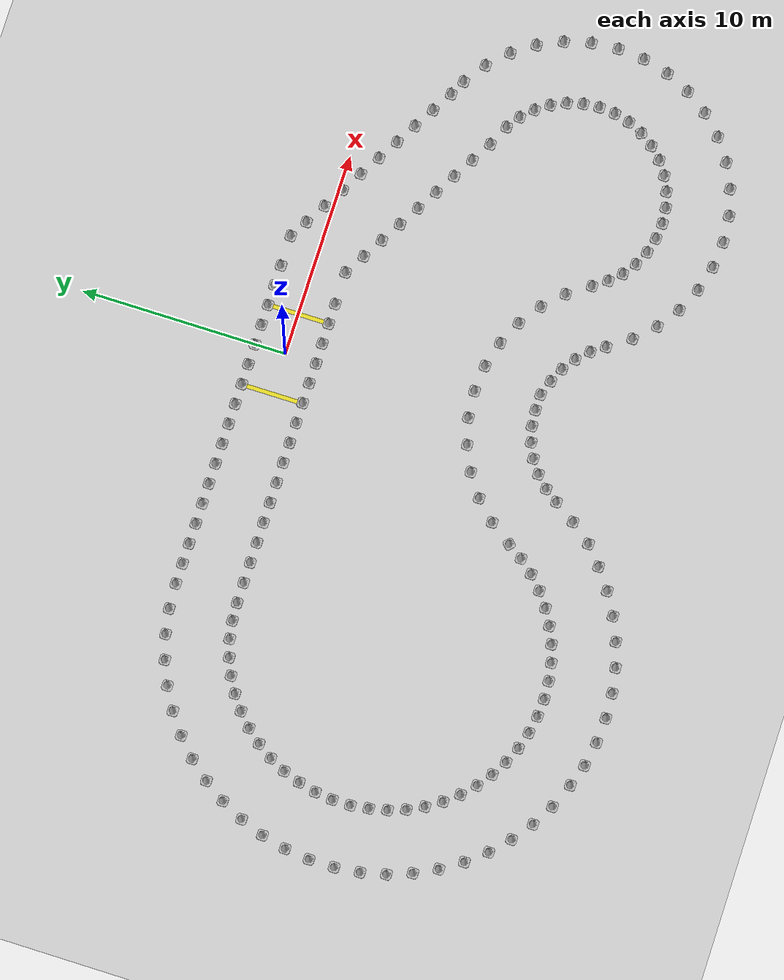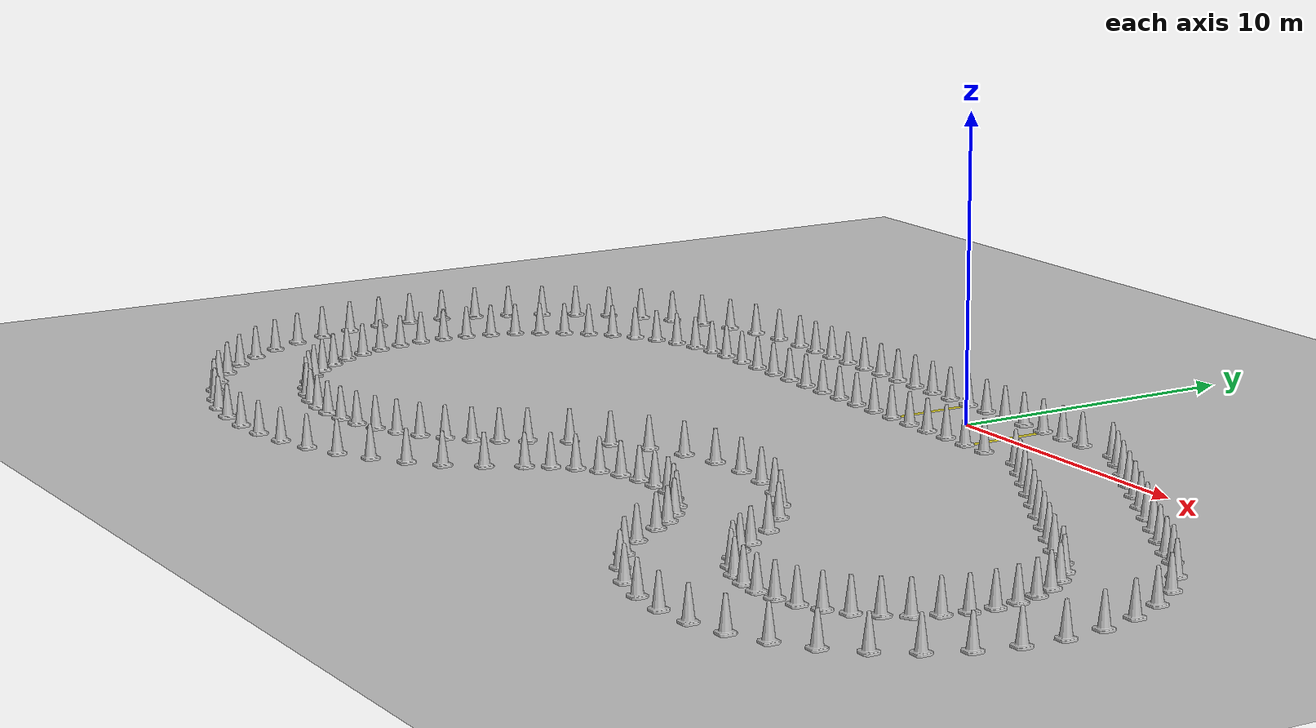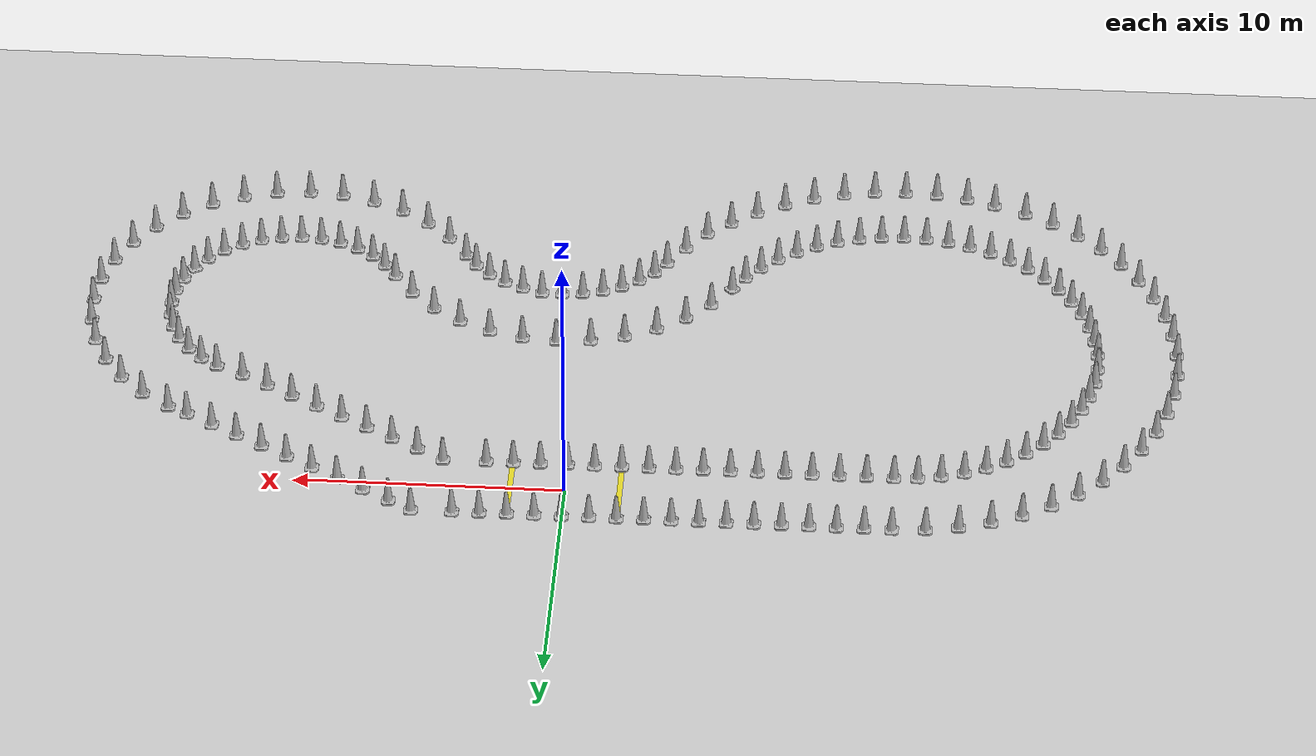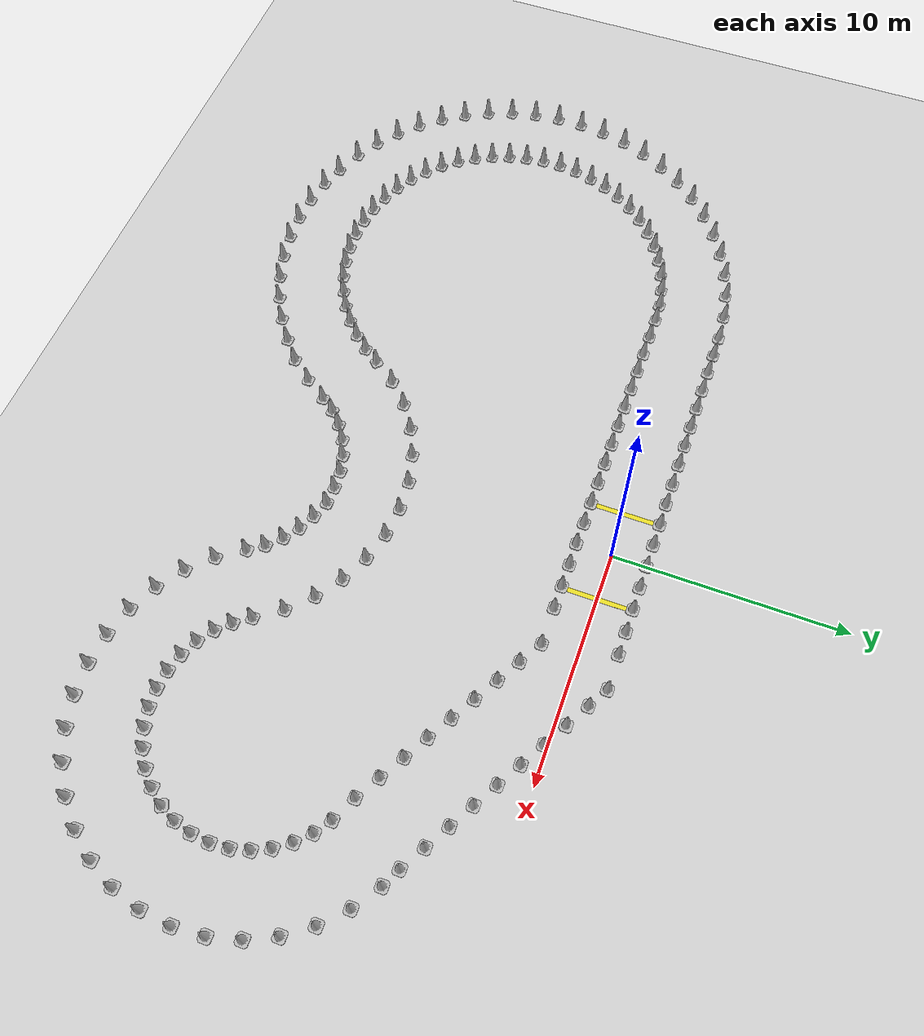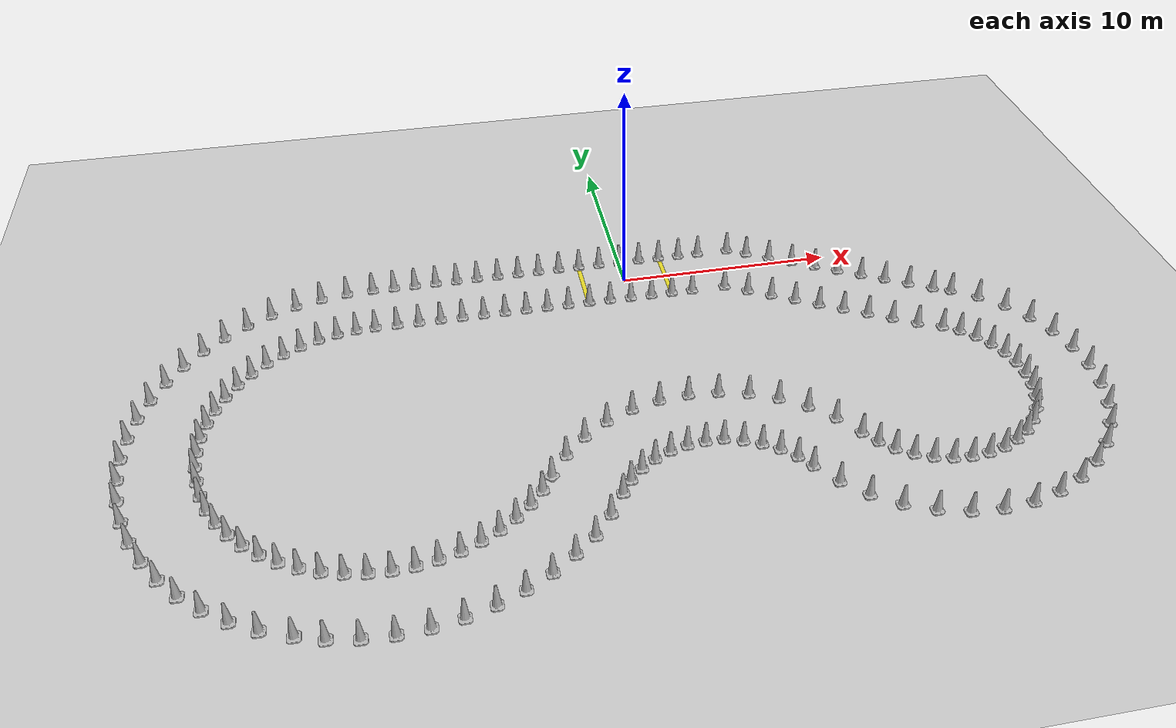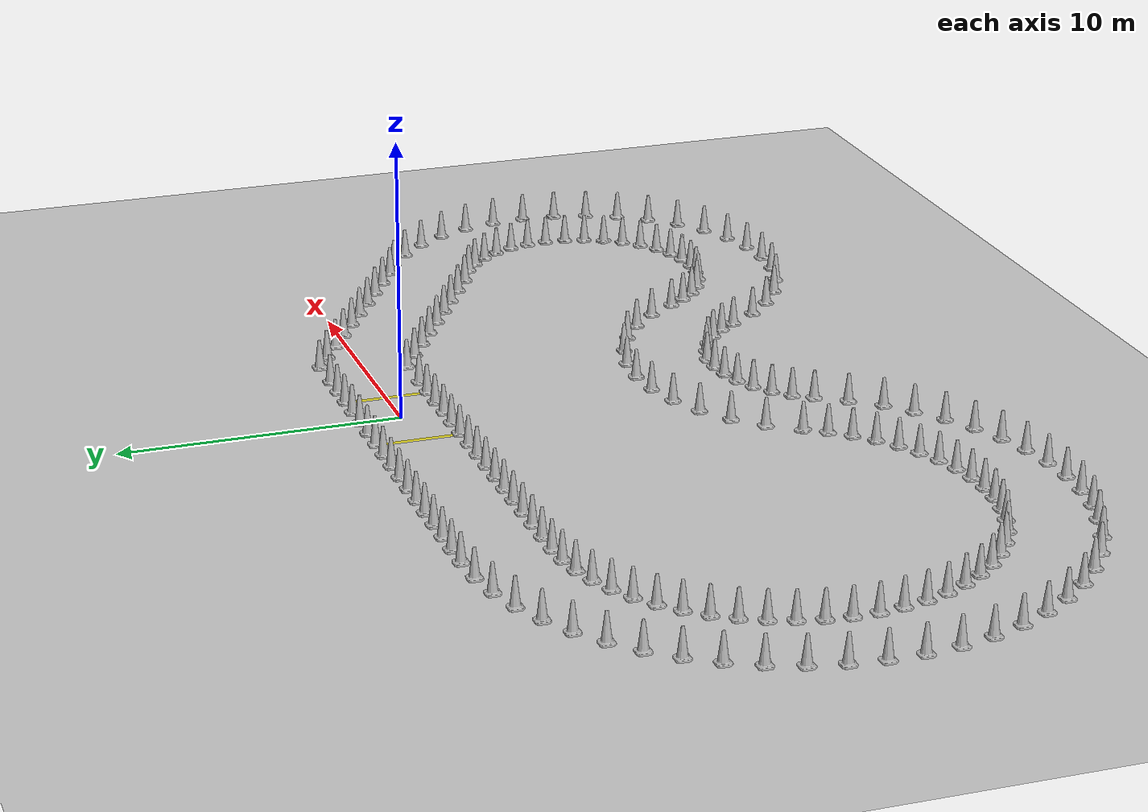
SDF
<sdf version="1.7">
 <world name="default">
  <light name="sun" type="directional">
   <pose>0 0 10 0 -0 0</pose>
   <diffuse>0.8 0.8 0.8 1</diffuse>
   <specular>0.2 0.2 0.2 1</specular>
   <attenuation>
    <range>1000</range>
    <constant>0.9</constant>
    <linear>0.01</linear>
    <quadratic>0.001</quadratic>
   </attenuation>
   <direction>-0.5 0.1 -0.9</direction>
   <spot><inner_angle>0</inner_angle><outer_angle>0</outer_angle><falloff>0</falloff></spot>
  </light>
  <model name="ground_plane">
   <static>1</static>
   <link name="link">
    <collision name="collision">
     <geometry><plane><normal>0 0 1</normal><size>100 100</size></plane></geometry>
     <surface><friction><ode><mu>100</mu><mu2>50</mu2></ode></friction></surface>
    </collision>
    <visual name="visual">
     <cast_shadows>0</cast_shadows>
     <geometry><plane><normal>0 0 1</normal><size>100 100</size></plane></geometry>
     <material>
      <script><uri>file://media/materials/scripts/gazebo.material</uri><name>Gazebo/Grey</name></script>
     </material>
    </visual>
   </link>
  </model>
  <gravity>0 0 -9.8</gravity>
  <magnetic_field>6e-06 2.3e-05 -4.2e-05</magnetic_field>
  <atmosphere type="adiabatic"/>
  <physics type="ode">
   <max_step_size>0.001</max_step_size>
   <real_time_factor>1</real_time_factor>
   <real_time_update_rate>1000</real_time_update_rate>
  </physics>
  <scene><ambient>0.4 0.4 0.4 1</ambient><background>0.7 0.7 0.7 1</background><shadows>1</shadows></scene>
  <spherical_coordinates>
   <surface_model>EARTH_WGS84</surface_model>
   <latitude_deg>0</latitude_deg>
   <longitude_deg>0</longitude_deg>
   <elevation>0</elevation>
   <heading_deg>0</heading_deg>
  </spherical_coordinates>
  <model name="Construction Cone">
   <link name="link">
    <collision name="collision">
     <geometry>
      <mesh><scale>10 10 10</scale><uri>model://construction_cone/meshes/construction_cone.dae</uri></mesh>
     </geometry>
    </collision>
    <visual name="visual">
     <geometry>
      <mesh><scale>10 10 10</scale><uri>model://construction_cone/meshes/construction_cone.dae</uri></mesh>
     </geometry>
    </visual>
    <inertial>
     <inertia><ixx>1</ixx><ixy>0</ixy><ixz>0</ixz><iyy>1</iyy><iyz>0</iyz><izz>1</izz></inertia>
     <mass>1</mass>
    </inertial>
   </link>
   <pose>15.61 -12.04 -0 -0 -0 -0</pose>
  </model>
  <model name="Construction Cone_clone">
   <link name="link">
    <collision name="collision">
     <geometry>
      <mesh><scale>10 10 10</scale><uri>model://construction_cone/meshes/construction_cone.dae</uri></mesh>
     </geometry>
    </collision>
    <visual name="visual">
     <geometry>
      <mesh><scale>10 10 10</scale><uri>model://construction_cone/meshes/construction_cone.dae</uri></mesh>
     </geometry>
    </visual>
    <inertial>
     <inertia><ixx>1</ixx><ixy>0</ixy><ixz>0</ixz><iyy>1</iyy><iyz>0</iyz><izz>1</izz></inertia>
     <mass>1</mass>
    </inertial>
   </link>
   <pose>8.6 -3.81 -0 -0 -0 -0</pose>
  </model>
  <model name="Construction Cone_clone_0">
   <link name="link">
    <collision name="collision">
     <geometry>
      <mesh><scale>10 10 10</scale><uri>model://construction_cone/meshes/construction_cone.dae</uri></mesh>
     </geometry>
    </collision>
    <visual name="visual">
     <geometry>
      <mesh><scale>10 10 10</scale><uri>model://construction_cone/meshes/construction_cone.dae</uri></mesh>
     </geometry>
    </visual>
    <inertial>
     <inertia><ixx>1</ixx><ixy>0</ixy><ixz>0</ixz><iyy>1</iyy><iyz>0</iyz><izz>1</izz></inertia>
     <mass>1</mass>
    </inertial>
   </link>
   <pose>15.88 -10.5 -0 -0 -0 -0</pose>
  </model>
  <model name="Construction Cone_clone_1">
   <link name="link">
    <collision name="collision">
     <geometry>
      <mesh><scale>10 10 10</scale><uri>model://construction_cone/meshes/construction_cone.dae</uri></mesh>
     </geometry>
    </collision>
    <visual name="visual">
     <geometry>
      <mesh><scale>10 10 10</scale><uri>model://construction_cone/meshes/construction_cone.dae</uri></mesh>
     </geometry>
    </visual>
    <inertial>
     <inertia><ixx>1</ixx><ixy>0</ixy><ixz>0</ixz><iyy>1</iyy><iyz>0</iyz><izz>1</izz></inertia>
     <mass>1</mass>
    </inertial>
   </link>
   <pose>7.6 -3.23 -0 -0 -0 -0</pose>
  </model>
  <model name="Construction Cone_clone_2">
   <link name="link">
    <collision name="collision">
     <geometry>
      <mesh><scale>10 10 10</scale><uri>model://construction_cone/meshes/construction_cone.dae</uri></mesh>
     </geometry>
    </collision>
    <visual name="visual">
     <geometry>
      <mesh><scale>10 10 10</scale><uri>model://construction_cone/meshes/construction_cone.dae</uri></mesh>
     </geometry>
    </visual>
    <inertial>
     <inertia><ixx>1</ixx><ixy>0</ixy><ixz>0</ixz><iyy>1</iyy><iyz>0</iyz><izz>1</izz></inertia>
     <mass>1</mass>
    </inertial>
   </link>
   <pose>15.81 -11.28 -0 -0 -0 -0</pose>
  </model>
  <model name="Construction Cone_clone_3">
   <link name="link">
    <collision name="collision">
     <geometry>
      <mesh><scale>10 10 10</scale><uri>model://construction_cone/meshes/construction_cone.dae</uri></mesh>
     </geometry>
    </collision>
    <visual name="visual">
     <geometry>
      <mesh><scale>10 10 10</scale><uri>model://construction_cone/meshes/construction_cone.dae</uri></mesh>
     </geometry>
    </visual>
    <inertial>
     <inertia><ixx>1</ixx><ixy>0</ixy><ixz>0</ixz><iyy>1</iyy><iyz>0</iyz><izz>1</izz></inertia>
     <mass>1</mass>
    </inertial>
   </link>
   <pose>6.6 -2.65 -0 -0 -0 -0</pose>
  </model>
  <model name="Construction Cone_clone_4">
   <link name="link">
    <collision name="collision">
     <geometry>
      <mesh><scale>10 10 10</scale><uri>model://construction_cone/meshes/construction_cone.dae</uri></mesh>
     </geometry>
    </collision>
    <visual name="visual">
     <geometry>
      <mesh><scale>10 10 10</scale><uri>model://construction_cone/meshes/construction_cone.dae</uri></mesh>
     </geometry>
    </visual>
    <inertial>
     <inertia><ixx>1</ixx><ixy>0</ixy><ixz>0</ixz><iyy>1</iyy><iyz>0</iyz><izz>1</izz></inertia>
     <mass>1</mass>
    </inertial>
   </link>
   <pose>15.81 -9.72 -0 -0 -0 -0</pose>
  </model>
  <model name="Construction Cone_clone_5">
   <link name="link">
    <collision name="collision">
     <geometry>
      <mesh><scale>10 10 10</scale><uri>model://construction_cone/meshes/construction_cone.dae</uri></mesh>
     </geometry>
    </collision>
    <visual name="visual">
     <geometry>
      <mesh><scale>10 10 10</scale><uri>model://construction_cone/meshes/construction_cone.dae</uri></mesh>
     </geometry>
    </visual>
    <inertial>
     <inertia><ixx>1</ixx><ixy>0</ixy><ixz>0</ixz><iyy>1</iyy><iyz>0</iyz><izz>1</izz></inertia>
     <mass>1</mass>
    </inertial>
   </link>
   <pose>5.6 -2.08 -0 0 -1e-06 0</pose>
  </model>
  <model name="Construction Cone_clone_6">
   <link name="link">
    <collision name="collision">
     <geometry>
      <mesh><scale>10 10 10</scale><uri>model://construction_cone/meshes/construction_cone.dae</uri></mesh>
     </geometry>
    </collision>
    <visual name="visual">
     <geometry>
      <mesh><scale>10 10 10</scale><uri>model://construction_cone/meshes/construction_cone.dae</uri></mesh>
     </geometry>
    </visual>
    <inertial>
     <inertia><ixx>1</ixx><ixy>0</ixy><ixz>0</ixz><iyy>1</iyy><iyz>0</iyz><izz>1</izz></inertia>
     <mass>1</mass>
    </inertial>
   </link>
   <pose>15.28 -8.25 -0 0 -1e-06 0</pose>
  </model>
  <model name="Construction Cone_clone_7">
   <link name="link">
    <collision name="collision">
     <geometry>
      <mesh><scale>10 10 10</scale><uri>model://construction_cone/meshes/construction_cone.dae</uri></mesh>
     </geometry>
    </collision>
    <visual name="visual">
     <geometry>
      <mesh><scale>10 10 10</scale><uri>model://construction_cone/meshes/construction_cone.dae</uri></mesh>
     </geometry>
    </visual>
    <inertial>
     <inertia><ixx>1</ixx><ixy>0</ixy><ixz>0</ixz><iyy>1</iyy><iyz>0</iyz><izz>1</izz></inertia>
     <mass>1</mass>
    </inertial>
   </link>
   <pose>4.6 -1.5 -0 -0 -0 -0</pose>
  </model>
  <model name="Construction Cone_clone_8">
   <link name="link">
    <collision name="collision">
     <geometry>
      <mesh><scale>10 10 10</scale><uri>model://construction_cone/meshes/construction_cone.dae</uri></mesh>
     </geometry>
    </collision>
    <visual name="visual">
     <geometry>
      <mesh><scale>10 10 10</scale><uri>model://construction_cone/meshes/construction_cone.dae</uri></mesh>
     </geometry>
    </visual>
    <inertial>
     <inertia><ixx>1</ixx><ixy>0</ixy><ixz>0</ixz><iyy>1</iyy><iyz>0</iyz><izz>1</izz></inertia>
     <mass>1</mass>
    </inertial>
   </link>
   <pose>14.83 -7.61 -0 -0 -0 -0</pose>
  </model>
  <model name="Construction Cone_clone_9">
   <link name="link">
    <collision name="collision">
     <geometry>
      <mesh><scale>10 10 10</scale><uri>model://construction_cone/meshes/construction_cone.dae</uri></mesh>
     </geometry>
    </collision>
    <visual name="visual">
     <geometry>
      <mesh><scale>10 10 10</scale><uri>model://construction_cone/meshes/construction_cone.dae</uri></mesh>
     </geometry>
    </visual>
    <inertial>
     <inertia><ixx>1</ixx><ixy>0</ixy><ixz>0</ixz><iyy>1</iyy><iyz>0</iyz><izz>1</izz></inertia>
     <mass>1</mass>
    </inertial>
   </link>
   <pose>13.63 -6.6 -0 -0 -0 -0</pose>
  </model>
  <model name="Construction Cone_clone_10">
   <link name="link">
    <collision name="collision">
     <geometry>
      <mesh><scale>10 10 10</scale><uri>model://construction_cone/meshes/construction_cone.dae</uri></mesh>
     </geometry>
    </collision>
    <visual name="visual">
     <geometry>
      <mesh><scale>10 10 10</scale><uri>model://construction_cone/meshes/construction_cone.dae</uri></mesh>
     </geometry>
    </visual>
    <inertial>
     <inertia><ixx>1</ixx><ixy>0</ixy><ixz>0</ixz><iyy>1</iyy><iyz>0</iyz><izz>1</izz></inertia>
     <mass>1</mass>
    </inertial>
   </link>
   <pose>14.28 -7.05 -0 -0 -0 -0</pose>
  </model>
  <model name="Construction Cone_clone_11">
   <link name="link">
    <collision name="collision">
     <geometry>
      <mesh><scale>10 10 10</scale><uri>model://construction_cone/meshes/construction_cone.dae</uri></mesh>
     </geometry>
    </collision>
    <visual name="visual">
     <geometry>
      <mesh><scale>10 10 10</scale><uri>model://construction_cone/meshes/construction_cone.dae</uri></mesh>
     </geometry>
    </visual>
    <inertial>
     <inertia><ixx>1</ixx><ixy>0</ixy><ixz>0</ixz><iyy>1</iyy><iyz>0</iyz><izz>1</izz></inertia>
     <mass>1</mass>
    </inertial>
   </link>
   <pose>15.61 -8.96 -0 -0 -0 -0</pose>
  </model>
  <model name="Construction Cone_clone_12">
   <link name="link">
    <collision name="collision">
     <geometry>
      <mesh><scale>10 10 10</scale><uri>model://construction_cone/meshes/construction_cone.dae</uri></mesh>
     </geometry>
    </collision>
    <visual name="visual">
     <geometry>
      <mesh><scale>10 10 10</scale><uri>model://construction_cone/meshes/construction_cone.dae</uri></mesh>
     </geometry>
    </visual>
    <inertial>
     <inertia><ixx>1</ixx><ixy>0</ixy><ixz>0</ixz><iyy>1</iyy><iyz>0</iyz><izz>1</izz></inertia>
     <mass>1</mass>
    </inertial>
   </link>
   <pose>15.2793 -12.7506 -0 0 -0 0.480187</pose>
  </model>
  <model name="Construction Cone_clone_13">
   <link name="link">
    <collision name="collision">
     <geometry>
      <mesh><scale>10 10 10</scale><uri>model://construction_cone/meshes/construction_cone.dae</uri></mesh>
     </geometry>
    </collision>
    <visual name="visual">
     <geometry>
      <mesh><scale>10 10 10</scale><uri>model://construction_cone/meshes/construction_cone.dae</uri></mesh>
     </geometry>
    </visual>
    <inertial>
     <inertia><ixx>1</ixx><ixy>0</ixy><ixz>0</ixz><iyy>1</iyy><iyz>0</iyz><izz>1</izz></inertia>
     <mass>1</mass>
    </inertial>
   </link>
   <pose>9.6 -4.39 -0 -0 -0 -0</pose>
  </model>
  <model name="Construction Cone_clone_14">
   <link name="link">
    <collision name="collision">
     <geometry>
      <mesh><scale>10 10 10</scale><uri>model://construction_cone/meshes/construction_cone.dae</uri></mesh>
     </geometry>
    </collision>
    <visual name="visual">
     <geometry>
      <mesh><scale>10 10 10</scale><uri>model://construction_cone/meshes/construction_cone.dae</uri></mesh>
     </geometry>
    </visual>
    <inertial>
     <inertia><ixx>1</ixx><ixy>0</ixy><ixz>0</ixz><iyy>1</iyy><iyz>0</iyz><izz>1</izz></inertia>
     <mass>1</mass>
    </inertial>
   </link>
   <pose>14.83 -13.39 -0 -0 -0 -0</pose>
  </model>
  <model name="Construction Cone_clone_15">
   <link name="link">
    <collision name="collision">
     <geometry>
      <mesh><scale>10 10 10</scale><uri>model://construction_cone/meshes/construction_cone.dae</uri></mesh>
     </geometry>
    </collision>
    <visual name="visual">
     <geometry>
      <mesh><scale>10 10 10</scale><uri>model://construction_cone/meshes/construction_cone.dae</uri></mesh>
     </geometry>
    </visual>
    <inertial>
     <inertia><ixx>1</ixx><ixy>0</ixy><ixz>0</ixz><iyy>1</iyy><iyz>0</iyz><izz>1</izz></inertia>
     <mass>1</mass>
    </inertial>
   </link>
   <pose>10.6 -4.96 -0 -0 -0 -0</pose>
  </model>
  <model name="Construction Cone_clone_16">
   <link name="link">
    <collision name="collision">
     <geometry>
      <mesh><scale>10 10 10</scale><uri>model://construction_cone/meshes/construction_cone.dae</uri></mesh>
     </geometry>
    </collision>
    <visual name="visual">
     <geometry>
      <mesh><scale>10 10 10</scale><uri>model://construction_cone/meshes/construction_cone.dae</uri></mesh>
     </geometry>
    </visual>
    <inertial>
     <inertia><ixx>1</ixx><ixy>0</ixy><ixz>0</ixz><iyy>1</iyy><iyz>0</iyz><izz>1</izz></inertia>
     <mass>1</mass>
    </inertial>
   </link>
   <pose>14.28 -13.95 -0 0 -1e-06 0</pose>
  </model>
  <model name="Construction Cone_clone_17">
   <link name="link">
    <collision name="collision">
     <geometry>
      <mesh><scale>10 10 10</scale><uri>model://construction_cone/meshes/construction_cone.dae</uri></mesh>
     </geometry>
    </collision>
    <visual name="visual">
     <geometry>
      <mesh><scale>10 10 10</scale><uri>model://construction_cone/meshes/construction_cone.dae</uri></mesh>
     </geometry>
    </visual>
    <inertial>
     <inertia><ixx>1</ixx><ixy>0</ixy><ixz>0</ixz><iyy>1</iyy><iyz>0</iyz><izz>1</izz></inertia>
     <mass>1</mass>
    </inertial>
   </link>
   <pose>11.6 -5.54 -0 -0 -0 -0</pose>
  </model>
  <model name="Construction Cone_clone_18">
   <link name="link">
    <collision name="collision">
     <geometry>
      <mesh><scale>10 10 10</scale><uri>model://construction_cone/meshes/construction_cone.dae</uri></mesh>
     </geometry>
    </collision>
    <visual name="visual">
     <geometry>
      <mesh><scale>10 10 10</scale><uri>model://construction_cone/meshes/construction_cone.dae</uri></mesh>
     </geometry>
    </visual>
    <inertial>
     <inertia><ixx>1</ixx><ixy>0</ixy><ixz>0</ixz><iyy>1</iyy><iyz>0</iyz><izz>1</izz></inertia>
     <mass>1</mass>
    </inertial>
   </link>
   <pose>13.63 -14.4 -1e-05 0 -0 0</pose>
  </model>
  <model name="Construction Cone_clone_19">
   <link name="link">
    <collision name="collision">
     <geometry>
      <mesh><scale>10 10 10</scale><uri>model://construction_cone/meshes/construction_cone.dae</uri></mesh>
     </geometry>
    </collision>
    <visual name="visual">
     <geometry>
      <mesh><scale>10 10 10</scale><uri>model://construction_cone/meshes/construction_cone.dae</uri></mesh>
     </geometry>
    </visual>
    <inertial>
     <inertia><ixx>1</ixx><ixy>0</ixy><ixz>0</ixz><iyy>1</iyy><iyz>0</iyz><izz>1</izz></inertia>
     <mass>1</mass>
    </inertial>
   </link>
   <pose>12.6 -6.12 -0 0 -1e-06 0</pose>
  </model>
  <model name="Construction Cone_clone_20">
   <link name="link">
    <collision name="collision">
     <geometry>
      <mesh><scale>10 10 10</scale><uri>model://construction_cone/meshes/construction_cone.dae</uri></mesh>
     </geometry>
    </collision>
    <visual name="visual">
     <geometry>
      <mesh><scale>10 10 10</scale><uri>model://construction_cone/meshes/construction_cone.dae</uri></mesh>
     </geometry>
    </visual>
    <inertial>
     <inertia><ixx>1</ixx><ixy>0</ixy><ixz>0</ixz><iyy>1</iyy><iyz>0</iyz><izz>1</izz></inertia>
     <mass>1</mass>
    </inertial>
   </link>
   <pose>12.92 -14.73 -0 -0 -0 -0</pose>
  </model>
  <model name="Construction Cone_clone_21">
   <link name="link">
    <collision name="collision">
     <geometry>
      <mesh><scale>10 10 10</scale><uri>model://construction_cone/meshes/construction_cone.dae</uri></mesh>
     </geometry>
    </collision>
    <visual name="visual">
     <geometry>
      <mesh><scale>10 10 10</scale><uri>model://construction_cone/meshes/construction_cone.dae</uri></mesh>
     </geometry>
    </visual>
    <inertial>
     <inertia><ixx>1</ixx><ixy>0</ixy><ixz>0</ixz><iyy>1</iyy><iyz>0</iyz><izz>1</izz></inertia>
     <mass>1</mass>
    </inertial>
   </link>
   <pose>6.74 -11.68 -0 0 -0 0.044512</pose>
  </model>
  <model name="Construction Cone_clone_22">
   <link name="link">
    <collision name="collision">
     <geometry>
      <mesh><scale>10 10 10</scale><uri>model://construction_cone/meshes/construction_cone.dae</uri></mesh>
     </geometry>
    </collision>
    <visual name="visual">
     <geometry>
      <mesh><scale>10 10 10</scale><uri>model://construction_cone/meshes/construction_cone.dae</uri></mesh>
     </geometry>
    </visual>
    <inertial>
     <inertia><ixx>1</ixx><ixy>0</ixy><ixz>0</ixz><iyy>1</iyy><iyz>0</iyz><izz>1</izz></inertia>
     <mass>1</mass>
    </inertial>
   </link>
   <pose>12.16 -14.93 -0 -0 -0 -0</pose>
  </model>
  <model name="Construction Cone_clone_23">
   <link name="link">
    <collision name="collision">
     <geometry>
      <mesh><scale>10 10 10</scale><uri>model://construction_cone/meshes/construction_cone.dae</uri></mesh>
     </geometry>
    </collision>
    <visual name="visual">
     <geometry>
      <mesh><scale>10 10 10</scale><uri>model://construction_cone/meshes/construction_cone.dae</uri></mesh>
     </geometry>
    </visual>
    <inertial>
     <inertia><ixx>1</ixx><ixy>0</ixy><ixz>0</ixz><iyy>1</iyy><iyz>0</iyz><izz>1</izz></inertia>
     <mass>1</mass>
    </inertial>
   </link>
   <pose>5.81 -10.75 -0 0 -1e-06 0</pose>
  </model>
  <model name="Construction Cone_clone_24">
   <link name="link">
    <collision name="collision">
     <geometry>
      <mesh><scale>10 10 10</scale><uri>model://construction_cone/meshes/construction_cone.dae</uri></mesh>
     </geometry>
    </collision>
    <visual name="visual">
     <geometry>
      <mesh><scale>10 10 10</scale><uri>model://construction_cone/meshes/construction_cone.dae</uri></mesh>
     </geometry>
    </visual>
    <inertial>
     <inertia><ixx>1</ixx><ixy>0</ixy><ixz>0</ixz><iyy>1</iyy><iyz>0</iyz><izz>1</izz></inertia>
     <mass>1</mass>
    </inertial>
   </link>
   <pose>11.38 -15 -1e-05 0 -0 0</pose>
  </model>
  <model name="Construction Cone_clone_25">
   <link name="link">
    <collision name="collision">
     <geometry>
      <mesh><scale>10 10 10</scale><uri>model://construction_cone/meshes/construction_cone.dae</uri></mesh>
     </geometry>
    </collision>
    <visual name="visual">
     <geometry>
      <mesh><scale>10 10 10</scale><uri>model://construction_cone/meshes/construction_cone.dae</uri></mesh>
     </geometry>
    </visual>
    <inertial>
     <inertia><ixx>1</ixx><ixy>0</ixy><ixz>0</ixz><iyy>1</iyy><iyz>0</iyz><izz>1</izz></inertia>
     <mass>1</mass>
    </inertial>
   </link>
   <pose>4.73996 -9.99998 -0 -0 -0 -0.001118</pose>
  </model>
  <model name="Construction Cone_clone_26">
   <link name="link">
    <collision name="collision">
     <geometry>
      <mesh><scale>10 10 10</scale><uri>model://construction_cone/meshes/construction_cone.dae</uri></mesh>
     </geometry>
    </collision>
    <visual name="visual">
     <geometry>
      <mesh><scale>10 10 10</scale><uri>model://construction_cone/meshes/construction_cone.dae</uri></mesh>
     </geometry>
    </visual>
    <inertial>
     <inertia><ixx>1</ixx><ixy>0</ixy><ixz>0</ixz><iyy>1</iyy><iyz>0</iyz><izz>1</izz></inertia>
     <mass>1</mass>
    </inertial>
   </link>
   <pose>10.6 -14.93 -0 -0 -0 -0</pose>
  </model>
  <model name="Construction Cone_clone_27">
   <link name="link">
    <collision name="collision">
     <geometry>
      <mesh><scale>10 10 10</scale><uri>model://construction_cone/meshes/construction_cone.dae</uri></mesh>
     </geometry>
    </collision>
    <visual name="visual">
     <geometry>
      <mesh><scale>10 10 10</scale><uri>model://construction_cone/meshes/construction_cone.dae</uri></mesh>
     </geometry>
    </visual>
    <inertial>
     <inertia><ixx>1</ixx><ixy>0</ixy><ixz>0</ixz><iyy>1</iyy><iyz>0</iyz><izz>1</izz></inertia>
     <mass>1</mass>
    </inertial>
   </link>
   <pose>3.56 -9.45 -0 0 -1e-06 0</pose>
  </model>
  <model name="Construction Cone_clone_28">
   <link name="link">
    <collision name="collision">
     <geometry>
      <mesh><scale>10 10 10</scale><uri>model://construction_cone/meshes/construction_cone.dae</uri></mesh>
     </geometry>
    </collision>
    <visual name="visual">
     <geometry>
      <mesh><scale>10 10 10</scale><uri>model://construction_cone/meshes/construction_cone.dae</uri></mesh>
     </geometry>
    </visual>
    <inertial>
     <inertia><ixx>1</ixx><ixy>0</ixy><ixz>0</ixz><iyy>1</iyy><iyz>0</iyz><izz>1</izz></inertia>
     <mass>1</mass>
    </inertial>
   </link>
   <pose>9.84 -14.73 -0 0 -1e-06 0</pose>
  </model>
  <model name="Construction Cone_clone_29">
   <link name="link">
    <collision name="collision">
     <geometry>
      <mesh><scale>10 10 10</scale><uri>model://construction_cone/meshes/construction_cone.dae</uri></mesh>
     </geometry>
    </collision>
    <visual name="visual">
     <geometry>
      <mesh><scale>10 10 10</scale><uri>model://construction_cone/meshes/construction_cone.dae</uri></mesh>
     </geometry>
    </visual>
    <inertial>
     <inertia><ixx>1</ixx><ixy>0</ixy><ixz>0</ixz><iyy>1</iyy><iyz>0</iyz><izz>1</izz></inertia>
     <mass>1</mass>
    </inertial>
   </link>
   <pose>2.29 -9.11 -0 -0 -0 -0</pose>
  </model>
  <model name="Construction Cone_clone_30">
   <link name="link">
    <collision name="collision">
     <geometry>
      <mesh><scale>10 10 10</scale><uri>model://construction_cone/meshes/construction_cone.dae</uri></mesh>
     </geometry>
    </collision>
    <visual name="visual">
     <geometry>
      <mesh><scale>10 10 10</scale><uri>model://construction_cone/meshes/construction_cone.dae</uri></mesh>
     </geometry>
    </visual>
    <inertial>
     <inertia><ixx>1</ixx><ixy>0</ixy><ixz>0</ixz><iyy>1</iyy><iyz>0</iyz><izz>1</izz></inertia>
     <mass>1</mass>
    </inertial>
   </link>
   <pose>8.49 -13.95 -0 -0 -0 -0</pose>
  </model>
  <model name="Construction Cone_clone_31">
   <link name="link">
    <collision name="collision">
     <geometry>
      <mesh><scale>10 10 10</scale><uri>model://construction_cone/meshes/construction_cone.dae</uri></mesh>
     </geometry>
    </collision>
    <visual name="visual">
     <geometry>
      <mesh><scale>10 10 10</scale><uri>model://construction_cone/meshes/construction_cone.dae</uri></mesh>
     </geometry>
    </visual>
    <inertial>
     <inertia><ixx>1</ixx><ixy>0</ixy><ixz>0</ixz><iyy>1</iyy><iyz>0</iyz><izz>1</izz></inertia>
     <mass>1</mass>
    </inertial>
   </link>
   <pose>9.13 -14.4 -0 -0 -0 -0</pose>
  </model>
  <model name="Construction Cone_clone_32">
   <link name="link">
    <collision name="collision">
     <geometry>
      <mesh><scale>10 10 10</scale><uri>model://construction_cone/meshes/construction_cone.dae</uri></mesh>
     </geometry>
    </collision>
    <visual name="visual">
     <geometry>
      <mesh><scale>10 10 10</scale><uri>model://construction_cone/meshes/construction_cone.dae</uri></mesh>
     </geometry>
    </visual>
    <inertial>
     <inertia><ixx>1</ixx><ixy>0</ixy><ixz>0</ixz><iyy>1</iyy><iyz>0</iyz><izz>1</izz></inertia>
     <mass>1</mass>
    </inertial>
   </link>
   <pose>-0.31 -9.11 -0 -0 -0 -0</pose>
  </model>
  <model name="Construction Cone_clone_33">
   <link name="link">
    <collision name="collision">
     <geometry>
      <mesh><scale>10 10 10</scale><uri>model://construction_cone/meshes/construction_cone.dae</uri></mesh>
     </geometry>
    </collision>
    <visual name="visual">
     <geometry>
      <mesh><scale>10 10 10</scale><uri>model://construction_cone/meshes/construction_cone.dae</uri></mesh>
     </geometry>
    </visual>
    <inertial>
     <inertia><ixx>1</ixx><ixy>0</ixy><ixz>0</ixz><iyy>1</iyy><iyz>0</iyz><izz>1</izz></inertia>
     <mass>1</mass>
    </inertial>
   </link>
   <pose>0.99 -9 -0 -0 -0 -0</pose>
  </model>
  <model name="Construction Cone_clone_34">
   <link name="link">
    <collision name="collision">
     <geometry>
      <mesh><scale>10 10 10</scale><uri>model://construction_cone/meshes/construction_cone.dae</uri></mesh>
     </geometry>
    </collision>
    <visual name="visual">
     <geometry>
      <mesh><scale>10 10 10</scale><uri>model://construction_cone/meshes/construction_cone.dae</uri></mesh>
     </geometry>
    </visual>
    <inertial>
     <inertia><ixx>1</ixx><ixy>0</ixy><ixz>0</ixz><iyy>1</iyy><iyz>0</iyz><izz>1</izz></inertia>
     <mass>1</mass>
    </inertial>
   </link>
   <pose>7.96913 -13.3975 -0 0 -1e-06 -0.004085</pose>
  </model>
  <model name="Construction Cone_clone_35">
   <link name="link">
    <collision name="collision">
     <geometry>
      <mesh><scale>10 10 10</scale><uri>model://construction_cone/meshes/construction_cone.dae</uri></mesh>
     </geometry>
    </collision>
    <visual name="visual">
     <geometry>
      <mesh><scale>10 10 10</scale><uri>model://construction_cone/meshes/construction_cone.dae</uri></mesh>
     </geometry>
    </visual>
    <inertial>
     <inertia><ixx>1</ixx><ixy>0</ixy><ixz>0</ixz><iyy>1</iyy><iyz>0</iyz><izz>1</izz></inertia>
     <mass>1</mass>
    </inertial>
   </link>
   <pose>-1.57 -9.45 -0 -0 -0 -0</pose>
  </model>
  <model name="Construction Cone_clone_36">
   <link name="link">
    <collision name="collision">
     <geometry>
      <mesh><scale>10 10 10</scale><uri>model://construction_cone/meshes/construction_cone.dae</uri></mesh>
     </geometry>
    </collision>
    <visual name="visual">
     <geometry>
      <mesh><scale>10 10 10</scale><uri>model://construction_cone/meshes/construction_cone.dae</uri></mesh>
     </geometry>
    </visual>
    <inertial>
     <inertia><ixx>1</ixx><ixy>0</ixy><ixz>0</ixz><iyy>1</iyy><iyz>0</iyz><izz>1</izz></inertia>
     <mass>1</mass>
    </inertial>
   </link>
   <pose>7.49 -12.75 -0 0 -1e-06 0</pose>
  </model>
  <model name="Construction Cone_clone_37">
   <link name="link">
    <collision name="collision">
     <geometry>
      <mesh><scale>10 10 10</scale><uri>model://construction_cone/meshes/construction_cone.dae</uri></mesh>
     </geometry>
    </collision>
    <visual name="visual">
     <geometry>
      <mesh><scale>10 10 10</scale><uri>model://construction_cone/meshes/construction_cone.dae</uri></mesh>
     </geometry>
    </visual>
    <inertial>
     <inertia><ixx>1</ixx><ixy>0</ixy><ixz>0</ixz><iyy>1</iyy><iyz>0</iyz><izz>1</izz></inertia>
     <mass>1</mass>
    </inertial>
   </link>
   <pose>-2.76 -10 -0 -0 -0 -0</pose>
  </model>
  <model name="Construction Cone_clone_38">
   <link name="link">
    <collision name="collision">
     <geometry>
      <mesh><scale>10 10 10</scale><uri>model://construction_cone/meshes/construction_cone.dae</uri></mesh>
     </geometry>
    </collision>
    <visual name="visual">
     <geometry>
      <mesh><scale>10 10 10</scale><uri>model://construction_cone/meshes/construction_cone.dae</uri></mesh>
     </geometry>
    </visual>
    <inertial>
     <inertia><ixx>1</ixx><ixy>0</ixy><ixz>0</ixz><iyy>1</iyy><iyz>0</iyz><izz>1</izz></inertia>
     <mass>1</mass>
    </inertial>
   </link>
   <pose>-4.75 -11.68 -9e-06 1e-06 -0 0</pose>
  </model>
  <model name="Construction Cone_clone_39">
   <link name="link">
    <collision name="collision">
     <geometry>
      <mesh><scale>10 10 10</scale><uri>model://construction_cone/meshes/construction_cone.dae</uri></mesh>
     </geometry>
    </collision>
    <visual name="visual">
     <geometry>
      <mesh><scale>10 10 10</scale><uri>model://construction_cone/meshes/construction_cone.dae</uri></mesh>
     </geometry>
    </visual>
    <inertial>
     <inertia><ixx>1</ixx><ixy>0</ixy><ixz>0</ixz><iyy>1</iyy><iyz>0</iyz><izz>1</izz></inertia>
     <mass>1</mass>
    </inertial>
   </link>
   <pose>-6.54 -14.15 -0 -0 -0 -0</pose>
  </model>
  <model name="Construction Cone_clone_40">
   <link name="link">
    <collision name="collision">
     <geometry>
      <mesh><scale>10 10 10</scale><uri>model://construction_cone/meshes/construction_cone.dae</uri></mesh>
     </geometry>
    </collision>
    <visual name="visual">
     <geometry>
      <mesh><scale>10 10 10</scale><uri>model://construction_cone/meshes/construction_cone.dae</uri></mesh>
     </geometry>
    </visual>
    <inertial>
     <inertia><ixx>1</ixx><ixy>0</ixy><ixz>0</ixz><iyy>1</iyy><iyz>0</iyz><izz>1</izz></inertia>
     <mass>1</mass>
    </inertial>
   </link>
   <pose>-14.57 -1.95 -0 0 -1e-06 0</pose>
  </model>
  <model name="Construction Cone_clone_42">
   <link name="link">
    <collision name="collision">
     <geometry>
      <mesh><scale>10 10 10</scale><uri>model://construction_cone/meshes/construction_cone.dae</uri></mesh>
     </geometry>
    </collision>
    <visual name="visual">
     <geometry>
      <mesh><scale>10 10 10</scale><uri>model://construction_cone/meshes/construction_cone.dae</uri></mesh>
     </geometry>
    </visual>
    <inertial>
     <inertia><ixx>1</ixx><ixy>0</ixy><ixz>0</ixz><iyy>1</iyy><iyz>0</iyz><izz>1</izz></inertia>
     <mass>1</mass>
    </inertial>
   </link>
   <pose>-17.46 -3.85 -0 -0 -0 -0</pose>
  </model>
  <model name="Construction Cone_clone_43">
   <link name="link">
    <collision name="collision">
     <geometry>
      <mesh><scale>10 10 10</scale><uri>model://construction_cone/meshes/construction_cone.dae</uri></mesh>
     </geometry>
    </collision>
    <visual name="visual">
     <geometry>
      <mesh><scale>10 10 10</scale><uri>model://construction_cone/meshes/construction_cone.dae</uri></mesh>
     </geometry>
    </visual>
    <inertial>
     <inertia><ixx>1</ixx><ixy>0</ixy><ixz>0</ixz><iyy>1</iyy><iyz>0</iyz><izz>1</izz></inertia>
     <mass>1</mass>
    </inertial>
   </link>
   <pose>-16.12 -2.73 -0 0 -1e-06 0</pose>
  </model>
  <model name="Construction Cone_clone_44">
   <link name="link">
    <collision name="collision">
     <geometry>
      <mesh><scale>10 10 10</scale><uri>model://construction_cone/meshes/construction_cone.dae</uri></mesh>
     </geometry>
    </collision>
    <visual name="visual">
     <geometry>
      <mesh><scale>10 10 10</scale><uri>model://construction_cone/meshes/construction_cone.dae</uri></mesh>
     </geometry>
    </visual>
    <inertial>
     <inertia><ixx>1</ixx><ixy>0</ixy><ixz>0</ixz><iyy>1</iyy><iyz>0</iyz><izz>1</izz></inertia>
     <mass>1</mass>
    </inertial>
   </link>
   <pose>-18.5 -5.25 -0 -0 -0 -0</pose>
  </model>
  <model name="Construction Cone_clone_45">
   <link name="link">
    <collision name="collision">
     <geometry>
      <mesh><scale>10 10 10</scale><uri>model://construction_cone/meshes/construction_cone.dae</uri></mesh>
     </geometry>
    </collision>
    <visual name="visual">
     <geometry>
      <mesh><scale>10 10 10</scale><uri>model://construction_cone/meshes/construction_cone.dae</uri></mesh>
     </geometry>
    </visual>
    <inertial>
     <inertia><ixx>1</ixx><ixy>0</ixy><ixz>0</ixz><iyy>1</iyy><iyz>0</iyz><izz>1</izz></inertia>
     <mass>1</mass>
    </inertial>
   </link>
   <pose>-18.02 -4.52 -0 -0 -0 -0</pose>
  </model>
  <model name="Construction Cone_clone_46">
   <link name="link">
    <collision name="collision">
     <geometry>
      <mesh><scale>10 10 10</scale><uri>model://construction_cone/meshes/construction_cone.dae</uri></mesh>
     </geometry>
    </collision>
    <visual name="visual">
     <geometry>
      <mesh><scale>10 10 10</scale><uri>model://construction_cone/meshes/construction_cone.dae</uri></mesh>
     </geometry>
    </visual>
    <inertial>
     <inertia><ixx>1</ixx><ixy>0</ixy><ixz>0</ixz><iyy>1</iyy><iyz>0</iyz><izz>1</izz></inertia>
     <mass>1</mass>
    </inertial>
   </link>
   <pose>-15.37 -2.3 -0 -0 -0 -0</pose>
  </model>
  <model name="Construction Cone_clone_47">
   <link name="link">
    <collision name="collision">
     <geometry>
      <mesh><scale>10 10 10</scale><uri>model://construction_cone/meshes/construction_cone.dae</uri></mesh>
     </geometry>
    </collision>
    <visual name="visual">
     <geometry>
      <mesh><scale>10 10 10</scale><uri>model://construction_cone/meshes/construction_cone.dae</uri></mesh>
     </geometry>
    </visual>
    <inertial>
     <inertia><ixx>1</ixx><ixy>0</ixy><ixz>0</ixz><iyy>1</iyy><iyz>0</iyz><izz>1</izz></inertia>
     <mass>1</mass>
    </inertial>
   </link>
   <pose>-13.73 -1.7 -0 -0 -0 -0</pose>
  </model>
  <model name="Construction Cone_clone_48">
   <link name="link">
    <collision name="collision">
     <geometry>
      <mesh><scale>10 10 10</scale><uri>model://construction_cone/meshes/construction_cone.dae</uri></mesh>
     </geometry>
    </collision>
    <visual name="visual">
     <geometry>
      <mesh><scale>10 10 10</scale><uri>model://construction_cone/meshes/construction_cone.dae</uri></mesh>
     </geometry>
    </visual>
    <inertial>
     <inertia><ixx>1</ixx><ixy>0</ixy><ixz>0</ixz><iyy>1</iyy><iyz>0</iyz><izz>1</izz></inertia>
     <mass>1</mass>
    </inertial>
   </link>
   <pose>-12.8698 -1.5497 -0 -0 -0 -0</pose>
  </model>
  <model name="Construction Cone_clone_49">
   <link name="link">
    <collision name="collision">
     <geometry>
      <mesh><scale>10 10 10</scale><uri>model://construction_cone/meshes/construction_cone.dae</uri></mesh>
     </geometry>
    </collision>
    <visual name="visual">
     <geometry>
      <mesh><scale>10 10 10</scale><uri>model://construction_cone/meshes/construction_cone.dae</uri></mesh>
     </geometry>
    </visual>
    <inertial>
     <inertia><ixx>1</ixx><ixy>0</ixy><ixz>0</ixz><iyy>1</iyy><iyz>0</iyz><izz>1</izz></inertia>
     <mass>1</mass>
    </inertial>
   </link>
   <pose>-12 -1.5 -9e-06 1e-06 -0 0</pose>
  </model>
  <model name="Construction Cone_clone_50">
   <link name="link">
    <collision name="collision">
     <geometry>
      <mesh><scale>10 10 10</scale><uri>model://construction_cone/meshes/construction_cone.dae</uri></mesh>
     </geometry>
    </collision>
    <visual name="visual">
     <geometry>
      <mesh><scale>10 10 10</scale><uri>model://construction_cone/meshes/construction_cone.dae</uri></mesh>
     </geometry>
    </visual>
    <inertial>
     <inertia><ixx>1</ixx><ixy>0</ixy><ixz>0</ixz><iyy>1</iyy><iyz>0</iyz><izz>1</izz></inertia>
     <mass>1</mass>
    </inertial>
   </link>
   <pose>-3.83 -10.75 -0 -0 -0 -0</pose>
  </model>
  <model name="Construction Cone_clone_51">
   <link name="link">
    <collision name="collision">
     <geometry>
      <mesh><scale>10 10 10</scale><uri>model://construction_cone/meshes/construction_cone.dae</uri></mesh>
     </geometry>
    </collision>
    <visual name="visual">
     <geometry>
      <mesh><scale>10 10 10</scale><uri>model://construction_cone/meshes/construction_cone.dae</uri></mesh>
     </geometry>
    </visual>
    <inertial>
     <inertia><ixx>1</ixx><ixy>0</ixy><ixz>0</ixz><iyy>1</iyy><iyz>0</iyz><izz>1</izz></inertia>
     <mass>1</mass>
    </inertial>
   </link>
   <pose>-16.82 -3.25 -0 -0 -0 -0</pose>
  </model>
  <model name="Construction Cone_clone_52">
   <link name="link">
    <collision name="collision">
     <geometry>
      <mesh><scale>10 10 10</scale><uri>model://construction_cone/meshes/construction_cone.dae</uri></mesh>
     </geometry>
    </collision>
    <visual name="visual">
     <geometry>
      <mesh><scale>10 10 10</scale><uri>model://construction_cone/meshes/construction_cone.dae</uri></mesh>
     </geometry>
    </visual>
    <inertial>
     <inertia><ixx>1</ixx><ixy>0</ixy><ixz>0</ixz><iyy>1</iyy><iyz>0</iyz><izz>1</izz></inertia>
     <mass>1</mass>
    </inertial>
   </link>
   <pose>-19.18 -6.85 -0 -0 -0 -0</pose>
  </model>
  <model name="Construction Cone_clone_53">
   <link name="link">
    <collision name="collision">
     <geometry>
      <mesh><scale>10 10 10</scale><uri>model://construction_cone/meshes/construction_cone.dae</uri></mesh>
     </geometry>
    </collision>
    <visual name="visual">
     <geometry>
      <mesh><scale>10 10 10</scale><uri>model://construction_cone/meshes/construction_cone.dae</uri></mesh>
     </geometry>
    </visual>
    <inertial>
     <inertia><ixx>1</ixx><ixy>0</ixy><ixz>0</ixz><iyy>1</iyy><iyz>0</iyz><izz>1</izz></inertia>
     <mass>1</mass>
    </inertial>
   </link>
   <pose>-19.39 -7.7 -0 -0 -0 -0</pose>
  </model>
  <model name="Construction Cone_clone_54">
   <link name="link">
    <collision name="collision">
     <geometry>
      <mesh><scale>10 10 10</scale><uri>model://construction_cone/meshes/construction_cone.dae</uri></mesh>
     </geometry>
    </collision>
    <visual name="visual">
     <geometry>
      <mesh><scale>10 10 10</scale><uri>model://construction_cone/meshes/construction_cone.dae</uri></mesh>
     </geometry>
    </visual>
    <inertial>
     <inertia><ixx>1</ixx><ixy>0</ixy><ixz>0</ixz><iyy>1</iyy><iyz>0</iyz><izz>1</izz></inertia>
     <mass>1</mass>
    </inertial>
   </link>
   <pose>-18.89 -6.03 -0 -0 -0 -0</pose>
  </model>
  <model name="Construction Cone_clone_55">
   <link name="link">
    <collision name="collision">
     <geometry>
      <mesh><scale>10 10 10</scale><uri>model://construction_cone/meshes/construction_cone.dae</uri></mesh>
     </geometry>
    </collision>
    <visual name="visual">
     <geometry>
      <mesh><scale>10 10 10</scale><uri>model://construction_cone/meshes/construction_cone.dae</uri></mesh>
     </geometry>
    </visual>
    <inertial>
     <inertia><ixx>1</ixx><ixy>0</ixy><ixz>0</ixz><iyy>1</iyy><iyz>0</iyz><izz>1</izz></inertia>
     <mass>1</mass>
    </inertial>
   </link>
   <pose>-19.369 -10.3 -0 -0 -0 -0</pose>
  </model>
  <model name="Construction Cone_clone_56">
   <link name="link">
    <collision name="collision">
     <geometry>
      <mesh><scale>10 10 10</scale><uri>model://construction_cone/meshes/construction_cone.dae</uri></mesh>
     </geometry>
    </collision>
    <visual name="visual">
     <geometry>
      <mesh><scale>10 10 10</scale><uri>model://construction_cone/meshes/construction_cone.dae</uri></mesh>
     </geometry>
    </visual>
    <inertial>
     <inertia><ixx>1</ixx><ixy>0</ixy><ixz>0</ixz><iyy>1</iyy><iyz>0</iyz><izz>1</izz></inertia>
     <mass>1</mass>
    </inertial>
   </link>
   <pose>-18.5 -12.75 -0 -0 -0 -0</pose>
  </model>
  <model name="Construction Cone_clone_57">
   <link name="link">
    <collision name="collision">
     <geometry>
      <mesh><scale>10 10 10</scale><uri>model://construction_cone/meshes/construction_cone.dae</uri></mesh>
     </geometry>
    </collision>
    <visual name="visual">
     <geometry>
      <mesh><scale>10 10 10</scale><uri>model://construction_cone/meshes/construction_cone.dae</uri></mesh>
     </geometry>
    </visual>
    <inertial>
     <inertia><ixx>1</ixx><ixy>0</ixy><ixz>0</ixz><iyy>1</iyy><iyz>0</iyz><izz>1</izz></inertia>
     <mass>1</mass>
    </inertial>
   </link>
   <pose>-18.02 -13.48 -0 -0 -0 -0</pose>
  </model>
  <model name="Construction Cone_clone_58">
   <link name="link">
    <collision name="collision">
     <geometry>
      <mesh><scale>10 10 10</scale><uri>model://construction_cone/meshes/construction_cone.dae</uri></mesh>
     </geometry>
    </collision>
    <visual name="visual">
     <geometry>
      <mesh><scale>10 10 10</scale><uri>model://construction_cone/meshes/construction_cone.dae</uri></mesh>
     </geometry>
    </visual>
    <inertial>
     <inertia><ixx>1</ixx><ixy>0</ixy><ixz>0</ixz><iyy>1</iyy><iyz>0</iyz><izz>1</izz></inertia>
     <mass>1</mass>
    </inertial>
   </link>
   <pose>-15.37 -15.7 -0 -0 -0 -0</pose>
  </model>
  <model name="Construction Cone_clone_59">
   <link name="link">
    <collision name="collision">
     <geometry>
      <mesh><scale>10 10 10</scale><uri>model://construction_cone/meshes/construction_cone.dae</uri></mesh>
     </geometry>
    </collision>
    <visual name="visual">
     <geometry>
      <mesh><scale>10 10 10</scale><uri>model://construction_cone/meshes/construction_cone.dae</uri></mesh>
     </geometry>
    </visual>
    <inertial>
     <inertia><ixx>1</ixx><ixy>0</ixy><ixz>0</ixz><iyy>1</iyy><iyz>0</iyz><izz>1</izz></inertia>
     <mass>1</mass>
    </inertial>
   </link>
   <pose>-12 -16.5 -0 0 -1e-06 0</pose>
  </model>
  <model name="Construction Cone_clone_60">
   <link name="link">
    <collision name="collision">
     <geometry>
      <mesh><scale>10 10 10</scale><uri>model://construction_cone/meshes/construction_cone.dae</uri></mesh>
     </geometry>
    </collision>
    <visual name="visual">
     <geometry>
      <mesh><scale>10 10 10</scale><uri>model://construction_cone/meshes/construction_cone.dae</uri></mesh>
     </geometry>
    </visual>
    <inertial>
     <inertia><ixx>1</ixx><ixy>0</ixy><ixz>0</ixz><iyy>1</iyy><iyz>0</iyz><izz>1</izz></inertia>
     <mass>1</mass>
    </inertial>
   </link>
   <pose>-10.27 -16.3 -0 -0 -0 -0</pose>
  </model>
  <model name="Construction Cone_clone_61">
   <link name="link">
    <collision name="collision">
     <geometry>
      <mesh><scale>10 10 10</scale><uri>model://construction_cone/meshes/construction_cone.dae</uri></mesh>
     </geometry>
    </collision>
    <visual name="visual">
     <geometry>
      <mesh><scale>10 10 10</scale><uri>model://construction_cone/meshes/construction_cone.dae</uri></mesh>
     </geometry>
    </visual>
    <inertial>
     <inertia><ixx>1</ixx><ixy>0</ixy><ixz>0</ixz><iyy>1</iyy><iyz>0</iyz><izz>1</izz></inertia>
     <mass>1</mass>
    </inertial>
   </link>
   <pose>-7.88 -15.27 -0 -0 -0 -0</pose>
  </model>
  <model name="Construction Cone_clone_62">
   <link name="link">
    <collision name="collision">
     <geometry>
      <mesh><scale>10 10 10</scale><uri>model://construction_cone/meshes/construction_cone.dae</uri></mesh>
     </geometry>
    </collision>
    <visual name="visual">
     <geometry>
      <mesh><scale>10 10 10</scale><uri>model://construction_cone/meshes/construction_cone.dae</uri></mesh>
     </geometry>
    </visual>
    <inertial>
     <inertia><ixx>1</ixx><ixy>0</ixy><ixz>0</ixz><iyy>1</iyy><iyz>0</iyz><izz>1</izz></inertia>
     <mass>1</mass>
    </inertial>
   </link>
   <pose>-7.18 -14.75 -0 -0 -0 -0</pose>
  </model>
  <model name="Construction Cone_clone_64">
   <link name="link">
    <collision name="collision">
     <geometry>
      <mesh><scale>10 10 10</scale><uri>model://construction_cone/meshes/construction_cone.dae</uri></mesh>
     </geometry>
    </collision>
    <visual name="visual">
     <geometry>
      <mesh><scale>10 10 10</scale><uri>model://construction_cone/meshes/construction_cone.dae</uri></mesh>
     </geometry>
    </visual>
    <inertial>
     <inertia><ixx>1</ixx><ixy>0</ixy><ixz>0</ixz><iyy>1</iyy><iyz>0</iyz><izz>1</izz></inertia>
     <mass>1</mass>
    </inertial>
   </link>
   <pose>-19.49 -8.56 -0 -0 -0 -0</pose>
  </model>
  <model name="Construction Cone_clone_65">
   <link name="link">
    <collision name="collision">
     <geometry>
      <mesh><scale>10 10 10</scale><uri>model://construction_cone/meshes/construction_cone.dae</uri></mesh>
     </geometry>
    </collision>
    <visual name="visual">
     <geometry>
      <mesh><scale>10 10 10</scale><uri>model://construction_cone/meshes/construction_cone.dae</uri></mesh>
     </geometry>
    </visual>
    <inertial>
     <inertia><ixx>1</ixx><ixy>0</ixy><ixz>0</ixz><iyy>1</iyy><iyz>0</iyz><izz>1</izz></inertia>
     <mass>1</mass>
    </inertial>
   </link>
   <pose>-19.49 -9.44 -0 -0 -0 -0</pose>
  </model>
  <model name="Construction Cone_clone_66">
   <link name="link">
    <collision name="collision">
     <geometry>
      <mesh><scale>10 10 10</scale><uri>model://construction_cone/meshes/construction_cone.dae</uri></mesh>
     </geometry>
    </collision>
    <visual name="visual">
     <geometry>
      <mesh><scale>10 10 10</scale><uri>model://construction_cone/meshes/construction_cone.dae</uri></mesh>
     </geometry>
    </visual>
    <inertial>
     <inertia><ixx>1</ixx><ixy>0</ixy><ixz>0</ixz><iyy>1</iyy><iyz>0</iyz><izz>1</izz></inertia>
     <mass>1</mass>
    </inertial>
   </link>
   <pose>-11.13 -16.45 -0 -0 -0 -0</pose>
  </model>
  <model name="Construction Cone_clone_67">
   <link name="link">
    <collision name="collision">
     <geometry>
      <mesh><scale>10 10 10</scale><uri>model://construction_cone/meshes/construction_cone.dae</uri></mesh>
     </geometry>
    </collision>
    <visual name="visual">
     <geometry>
      <mesh><scale>10 10 10</scale><uri>model://construction_cone/meshes/construction_cone.dae</uri></mesh>
     </geometry>
    </visual>
    <inertial>
     <inertia><ixx>1</ixx><ixy>0</ixy><ixz>0</ixz><iyy>1</iyy><iyz>0</iyz><izz>1</izz></inertia>
     <mass>1</mass>
    </inertial>
   </link>
   <pose>-12.87 -16.45 -1e-05 0 -0 0</pose>
  </model>
  <model name="Construction Cone_clone_68">
   <link name="link">
    <collision name="collision">
     <geometry>
      <mesh><scale>10 10 10</scale><uri>model://construction_cone/meshes/construction_cone.dae</uri></mesh>
     </geometry>
    </collision>
    <visual name="visual">
     <geometry>
      <mesh><scale>10 10 10</scale><uri>model://construction_cone/meshes/construction_cone.dae</uri></mesh>
     </geometry>
    </visual>
    <inertial>
     <inertia><ixx>1</ixx><ixy>0</ixy><ixz>0</ixz><iyy>1</iyy><iyz>0</iyz><izz>1</izz></inertia>
     <mass>1</mass>
    </inertial>
   </link>
   <pose>-14.57 -16.05 -0 -0 -0 -0</pose>
  </model>
  <model name="Construction Cone_clone_69">
   <link name="link">
    <collision name="collision">
     <geometry>
      <mesh><scale>10 10 10</scale><uri>model://construction_cone/meshes/construction_cone.dae</uri></mesh>
     </geometry>
    </collision>
    <visual name="visual">
     <geometry>
      <mesh><scale>10 10 10</scale><uri>model://construction_cone/meshes/construction_cone.dae</uri></mesh>
     </geometry>
    </visual>
    <inertial>
     <inertia><ixx>1</ixx><ixy>0</ixy><ixz>0</ixz><iyy>1</iyy><iyz>0</iyz><izz>1</izz></inertia>
     <mass>1</mass>
    </inertial>
   </link>
   <pose>-16.82 -14.75 -0 -0 -0 -0</pose>
  </model>
  <model name="Construction Cone_clone_70">
   <link name="link">
    <collision name="collision">
     <geometry>
      <mesh><scale>10 10 10</scale><uri>model://construction_cone/meshes/construction_cone.dae</uri></mesh>
     </geometry>
    </collision>
    <visual name="visual">
     <geometry>
      <mesh><scale>10 10 10</scale><uri>model://construction_cone/meshes/construction_cone.dae</uri></mesh>
     </geometry>
    </visual>
    <inertial>
     <inertia><ixx>1</ixx><ixy>0</ixy><ixz>0</ixz><iyy>1</iyy><iyz>0</iyz><izz>1</izz></inertia>
     <mass>1</mass>
    </inertial>
   </link>
   <pose>-17.46 -14.15 -0 -0 -0 -0</pose>
  </model>
  <model name="Construction Cone_clone_71">
   <link name="link">
    <collision name="collision">
     <geometry>
      <mesh><scale>10 10 10</scale><uri>model://construction_cone/meshes/construction_cone.dae</uri></mesh>
     </geometry>
    </collision>
    <visual name="visual">
     <geometry>
      <mesh><scale>10 10 10</scale><uri>model://construction_cone/meshes/construction_cone.dae</uri></mesh>
     </geometry>
    </visual>
    <inertial>
     <inertia><ixx>1</ixx><ixy>0</ixy><ixz>0</ixz><iyy>1</iyy><iyz>0</iyz><izz>1</izz></inertia>
     <mass>1</mass>
    </inertial>
   </link>
   <pose>-18.89 -11.97 -0 -0 -0 -0</pose>
  </model>
  <model name="Construction Cone_clone_72">
   <link name="link">
    <collision name="collision">
     <geometry>
      <mesh><scale>10 10 10</scale><uri>model://construction_cone/meshes/construction_cone.dae</uri></mesh>
     </geometry>
    </collision>
    <visual name="visual">
     <geometry>
      <mesh><scale>10 10 10</scale><uri>model://construction_cone/meshes/construction_cone.dae</uri></mesh>
     </geometry>
    </visual>
    <inertial>
     <inertia><ixx>1</ixx><ixy>0</ixy><ixz>0</ixz><iyy>1</iyy><iyz>0</iyz><izz>1</izz></inertia>
     <mass>1</mass>
    </inertial>
   </link>
   <pose>-19.18 -11.15 -0 -0 -0 -0</pose>
  </model>
  <model name="Construction Cone_clone_73">
   <link name="link">
    <collision name="collision">
     <geometry>
      <mesh><scale>10 10 10</scale><uri>model://construction_cone/meshes/construction_cone.dae</uri></mesh>
     </geometry>
    </collision>
    <visual name="visual">
     <geometry>
      <mesh><scale>10 10 10</scale><uri>model://construction_cone/meshes/construction_cone.dae</uri></mesh>
     </geometry>
    </visual>
    <inertial>
     <inertia><ixx>1</ixx><ixy>0</ixy><ixz>0</ixz><iyy>1</iyy><iyz>0</iyz><izz>1</izz></inertia>
     <mass>1</mass>
    </inertial>
   </link>
   <pose>-16.12 -15.27 -0 -0 -0 -0</pose>
  </model>
  <model name="Construction Cone_clone_74">
   <link name="link">
    <collision name="collision">
     <geometry>
      <mesh><scale>10 10 10</scale><uri>model://construction_cone/meshes/construction_cone.dae</uri></mesh>
     </geometry>
    </collision>
    <visual name="visual">
     <geometry>
      <mesh><scale>10 10 10</scale><uri>model://construction_cone/meshes/construction_cone.dae</uri></mesh>
     </geometry>
    </visual>
    <inertial>
     <inertia><ixx>1</ixx><ixy>0</ixy><ixz>0</ixz><iyy>1</iyy><iyz>0</iyz><izz>1</izz></inertia>
     <mass>1</mass>
    </inertial>
   </link>
   <pose>-13.73 -16.3 -0 -0 -0 -0</pose>
  </model>
  <model name="Construction Cone_clone_75">
   <link name="link">
    <collision name="collision">
     <geometry>
      <mesh><scale>10 10 10</scale><uri>model://construction_cone/meshes/construction_cone.dae</uri></mesh>
     </geometry>
    </collision>
    <visual name="visual">
     <geometry>
      <mesh><scale>10 10 10</scale><uri>model://construction_cone/meshes/construction_cone.dae</uri></mesh>
     </geometry>
    </visual>
    <inertial>
     <inertia><ixx>1</ixx><ixy>0</ixy><ixz>0</ixz><iyy>1</iyy><iyz>0</iyz><izz>1</izz></inertia>
     <mass>1</mass>
    </inertial>
   </link>
   <pose>-9.43 -16.05 -0 -0 -0 -0</pose>
  </model>
  <model name="Construction Cone_clone_76">
   <link name="link">
    <collision name="collision">
     <geometry>
      <mesh><scale>10 10 10</scale><uri>model://construction_cone/meshes/construction_cone.dae</uri></mesh>
     </geometry>
    </collision>
    <visual name="visual">
     <geometry>
      <mesh><scale>10 10 10</scale><uri>model://construction_cone/meshes/construction_cone.dae</uri></mesh>
     </geometry>
    </visual>
    <inertial>
     <inertia><ixx>1</ixx><ixy>0</ixy><ixz>0</ixz><iyy>1</iyy><iyz>0</iyz><izz>1</izz></inertia>
     <mass>1</mass>
    </inertial>
   </link>
   <pose>-8.63 -15.7 -0 -0 -0 -0</pose>
  </model>
  <model name="Construction Cone_clone_77">
   <link name="link">
    <collision name="collision">
     <geometry>
      <mesh><scale>10 10 10</scale><uri>model://construction_cone/meshes/construction_cone.dae</uri></mesh>
     </geometry>
    </collision>
    <visual name="visual">
     <geometry>
      <mesh><scale>10 10 10</scale><uri>model://construction_cone/meshes/construction_cone.dae</uri></mesh>
     </geometry>
    </visual>
    <inertial>
     <inertia><ixx>1</ixx><ixy>0</ixy><ixz>0</ixz><iyy>1</iyy><iyz>0</iyz><izz>1</izz></inertia>
     <mass>1</mass>
    </inertial>
   </link>
   <pose>-5.98 -13.48 -0 0 -0 0.005676</pose>
  </model>
  <model name="Construction Cone_clone_78">
   <link name="link">
    <collision name="collision">
     <geometry>
      <mesh><scale>10 10 10</scale><uri>model://construction_cone/meshes/construction_cone.dae</uri></mesh>
     </geometry>
    </collision>
    <visual name="visual">
     <geometry>
      <mesh><scale>10 10 10</scale><uri>model://construction_cone/meshes/construction_cone.dae</uri></mesh>
     </geometry>
    </visual>
    <inertial>
     <inertia><ixx>1</ixx><ixy>0</ixy><ixz>0</ixz><iyy>1</iyy><iyz>0</iyz><izz>1</izz></inertia>
     <mass>1</mass>
    </inertial>
   </link>
   <pose>-5.5 -12.75 -0 0 -0 0.778719</pose>
  </model>
  <model name="Construction Cone_clone_79">
   <link name="link">
    <collision name="collision">
     <geometry>
      <mesh><scale>10 10 10</scale><uri>model://construction_cone/meshes/construction_cone.dae</uri></mesh>
     </geometry>
    </collision>
    <visual name="visual">
     <geometry>
      <mesh><scale>10 10 10</scale><uri>model://construction_cone/meshes/construction_cone.dae</uri></mesh>
     </geometry>
    </visual>
    <inertial>
     <inertia><ixx>1</ixx><ixy>0</ixy><ixz>0</ixz><iyy>1</iyy><iyz>0</iyz><izz>1</izz></inertia>
     <mass>1</mass>
    </inertial>
   </link>
   <pose>1 -1.5 -0 -0 -0 -0</pose>
  </model>
  <model name="Construction Cone_clone_80">
   <link name="link">
    <collision name="collision">
     <geometry>
      <mesh><scale>10 10 10</scale><uri>model://construction_cone/meshes/construction_cone.dae</uri></mesh>
     </geometry>
    </collision>
    <visual name="visual">
     <geometry>
      <mesh><scale>10 10 10</scale><uri>model://construction_cone/meshes/construction_cone.dae</uri></mesh>
     </geometry>
    </visual>
    <inertial>
     <inertia><ixx>1</ixx><ixy>0</ixy><ixz>0</ixz><iyy>1</iyy><iyz>0</iyz><izz>1</izz></inertia>
     <mass>1</mass>
    </inertial>
   </link>
   <pose>-9 -1.5 -9e-06 1e-06 -0 0</pose>
  </model>
  <model name="Construction Cone_clone_81">
   <link name="link">
    <collision name="collision">
     <geometry>
      <mesh><scale>10 10 10</scale><uri>model://construction_cone/meshes/construction_cone.dae</uri></mesh>
     </geometry>
    </collision>
    <visual name="visual">
     <geometry>
      <mesh><scale>10 10 10</scale><uri>model://construction_cone/meshes/construction_cone.dae</uri></mesh>
     </geometry>
    </visual>
    <inertial>
     <inertia><ixx>1</ixx><ixy>0</ixy><ixz>0</ixz><iyy>1</iyy><iyz>0</iyz><izz>1</izz></inertia>
     <mass>1</mass>
    </inertial>
   </link>
   <pose>-10 -1.5 -0 -0 -0 -0</pose>
  </model>
  <model name="Construction Cone_clone_82">
   <link name="link">
    <collision name="collision">
     <geometry>
      <mesh><scale>10 10 10</scale><uri>model://construction_cone/meshes/construction_cone.dae</uri></mesh>
     </geometry>
    </collision>
    <visual name="visual">
     <geometry>
      <mesh><scale>10 10 10</scale><uri>model://construction_cone/meshes/construction_cone.dae</uri></mesh>
     </geometry>
    </visual>
    <inertial>
     <inertia><ixx>1</ixx><ixy>0</ixy><ixz>0</ixz><iyy>1</iyy><iyz>0</iyz><izz>1</izz></inertia>
     <mass>1</mass>
    </inertial>
   </link>
   <pose>1.99969 -1.50035 -0 0 -0 0.002407</pose>
  </model>
  <model name="Construction Cone_clone_83">
   <link name="link">
    <collision name="collision">
     <geometry>
      <mesh><scale>10 10 10</scale><uri>model://construction_cone/meshes/construction_cone.dae</uri></mesh>
     </geometry>
    </collision>
    <visual name="visual">
     <geometry>
      <mesh><scale>10 10 10</scale><uri>model://construction_cone/meshes/construction_cone.dae</uri></mesh>
     </geometry>
    </visual>
    <inertial>
     <inertia><ixx>1</ixx><ixy>0</ixy><ixz>0</ixz><iyy>1</iyy><iyz>0</iyz><izz>1</izz></inertia>
     <mass>1</mass>
    </inertial>
   </link>
   <pose>2.99996 -1.49992 -0 -0 -0 -0.001846</pose>
  </model>
  <model name="Construction Cone_clone_84">
   <link name="link">
    <collision name="collision">
     <geometry>
      <mesh><scale>10 10 10</scale><uri>model://construction_cone/meshes/construction_cone.dae</uri></mesh>
     </geometry>
    </collision>
    <visual name="visual">
     <geometry>
      <mesh><scale>10 10 10</scale><uri>model://construction_cone/meshes/construction_cone.dae</uri></mesh>
     </geometry>
    </visual>
    <inertial>
     <inertia><ixx>1</ixx><ixy>0</ixy><ixz>0</ixz><iyy>1</iyy><iyz>0</iyz><izz>1</izz></inertia>
     <mass>1</mass>
    </inertial>
   </link>
   <pose>-8 -1.5 -0 -0 -0 -0</pose>
  </model>
  <model name="Construction Cone_clone_85">
   <link name="link">
    <collision name="collision">
     <geometry>
      <mesh><scale>10 10 10</scale><uri>model://construction_cone/meshes/construction_cone.dae</uri></mesh>
     </geometry>
    </collision>
    <visual name="visual">
     <geometry>
      <mesh><scale>10 10 10</scale><uri>model://construction_cone/meshes/construction_cone.dae</uri></mesh>
     </geometry>
    </visual>
    <inertial>
     <inertia><ixx>1</ixx><ixy>0</ixy><ixz>0</ixz><iyy>1</iyy><iyz>0</iyz><izz>1</izz></inertia>
     <mass>1</mass>
    </inertial>
   </link>
   <pose>-3 -1.5 -9e-06 1e-06 -0 0</pose>
  </model>
  <model name="Construction Cone_clone_86">
   <link name="link">
    <collision name="collision">
     <geometry>
      <mesh><scale>10 10 10</scale><uri>model://construction_cone/meshes/construction_cone.dae</uri></mesh>
     </geometry>
    </collision>
    <visual name="visual">
     <geometry>
      <mesh><scale>10 10 10</scale><uri>model://construction_cone/meshes/construction_cone.dae</uri></mesh>
     </geometry>
    </visual>
    <inertial>
     <inertia><ixx>1</ixx><ixy>0</ixy><ixz>0</ixz><iyy>1</iyy><iyz>0</iyz><izz>1</izz></inertia>
     <mass>1</mass>
    </inertial>
   </link>
   <pose>0.000477 -1.51731 -0 -0 -0 -0.000491</pose>
  </model>
  <model name="Construction Cone_clone_87">
   <link name="link">
    <collision name="collision">
     <geometry>
      <mesh><scale>10 10 10</scale><uri>model://construction_cone/meshes/construction_cone.dae</uri></mesh>
     </geometry>
    </collision>
    <visual name="visual">
     <geometry>
      <mesh><scale>10 10 10</scale><uri>model://construction_cone/meshes/construction_cone.dae</uri></mesh>
     </geometry>
    </visual>
    <inertial>
     <inertia><ixx>1</ixx><ixy>0</ixy><ixz>0</ixz><iyy>1</iyy><iyz>0</iyz><izz>1</izz></inertia>
     <mass>1</mass>
    </inertial>
   </link>
   <pose>-2 -1.5 -0 -0 -0 -0</pose>
  </model>
  <model name="Construction Cone_clone_88">
   <link name="link">
    <collision name="collision">
     <geometry>
      <mesh><scale>10 10 10</scale><uri>model://construction_cone/meshes/construction_cone.dae</uri></mesh>
     </geometry>
    </collision>
    <visual name="visual">
     <geometry>
      <mesh><scale>10 10 10</scale><uri>model://construction_cone/meshes/construction_cone.dae</uri></mesh>
     </geometry>
    </visual>
    <inertial>
     <inertia><ixx>1</ixx><ixy>0</ixy><ixz>0</ixz><iyy>1</iyy><iyz>0</iyz><izz>1</izz></inertia>
     <mass>1</mass>
    </inertial>
   </link>
   <pose>-7.00024 -1.49975 -0 -0 -0 -0.009773</pose>
  </model>
  <model name="Construction Cone_clone_89">
   <link name="link">
    <collision name="collision">
     <geometry>
      <mesh><scale>10 10 10</scale><uri>model://construction_cone/meshes/construction_cone.dae</uri></mesh>
     </geometry>
    </collision>
    <visual name="visual">
     <geometry>
      <mesh><scale>10 10 10</scale><uri>model://construction_cone/meshes/construction_cone.dae</uri></mesh>
     </geometry>
    </visual>
    <inertial>
     <inertia><ixx>1</ixx><ixy>0</ixy><ixz>0</ixz><iyy>1</iyy><iyz>0</iyz><izz>1</izz></inertia>
     <mass>1</mass>
    </inertial>
   </link>
   <pose>-4 -1.5 -0 -0 -0 -0</pose>
  </model>
  <model name="Construction Cone_clone_90">
   <link name="link">
    <collision name="collision">
     <geometry>
      <mesh><scale>10 10 10</scale><uri>model://construction_cone/meshes/construction_cone.dae</uri></mesh>
     </geometry>
    </collision>
    <visual name="visual">
     <geometry>
      <mesh><scale>10 10 10</scale><uri>model://construction_cone/meshes/construction_cone.dae</uri></mesh>
     </geometry>
    </visual>
    <inertial>
     <inertia><ixx>1</ixx><ixy>0</ixy><ixz>0</ixz><iyy>1</iyy><iyz>0</iyz><izz>1</izz></inertia>
     <mass>1</mass>
    </inertial>
   </link>
   <pose>-4.99999 -1.50001 -0 1e-06 0 5.3e-05</pose>
  </model>
  <model name="Construction Cone_clone_91">
   <link name="link">
    <collision name="collision">
     <geometry>
      <mesh><scale>10 10 10</scale><uri>model://construction_cone/meshes/construction_cone.dae</uri></mesh>
     </geometry>
    </collision>
    <visual name="visual">
     <geometry>
      <mesh><scale>10 10 10</scale><uri>model://construction_cone/meshes/construction_cone.dae</uri></mesh>
     </geometry>
    </visual>
    <inertial>
     <inertia><ixx>1</ixx><ixy>0</ixy><ixz>0</ixz><iyy>1</iyy><iyz>0</iyz><izz>1</izz></inertia>
     <mass>1</mass>
    </inertial>
   </link>
   <pose>-6 -1.5 -0 0 -0 9e-06</pose>
  </model>
  <model name="Construction Cone_clone_92">
   <link name="link">
    <collision name="collision">
     <geometry>
      <mesh><scale>10 10 10</scale><uri>model://construction_cone/meshes/construction_cone.dae</uri></mesh>
     </geometry>
    </collision>
    <visual name="visual">
     <geometry>
      <mesh><scale>10 10 10</scale><uri>model://construction_cone/meshes/construction_cone.dae</uri></mesh>
     </geometry>
    </visual>
    <inertial>
     <inertia><ixx>1</ixx><ixy>0</ixy><ixz>0</ixz><iyy>1</iyy><iyz>0</iyz><izz>1</izz></inertia>
     <mass>1</mass>
    </inertial>
   </link>
   <pose>-1.00011 -1.49999 -0 0 -0 0.000433</pose>
  </model>
  <model name="Construction Cone_clone_63">
   <link name="link">
    <collision name="collision">
     <geometry>
      <mesh><scale>10 10 10</scale><uri>model://construction_cone/meshes/construction_cone.dae</uri></mesh>
     </geometry>
    </collision>
    <visual name="visual">
     <geometry>
      <mesh><scale>10 10 10</scale><uri>model://construction_cone/meshes/construction_cone.dae</uri></mesh>
     </geometry>
    </visual>
    <inertial>
     <inertia><ixx>1</ixx><ixy>0</ixy><ixz>0</ixz><iyy>1</iyy><iyz>0</iyz><izz>1</izz></inertia>
     <mass>1</mass>
    </inertial>
   </link>
   <pose>-11 -1.5 -9e-06 1e-06 -0 0</pose>
  </model>
  <model name="Construction Cone_clone_94">
   <link name="link">
    <collision name="collision">
     <geometry>
      <mesh><scale>10 10 10</scale><uri>model://construction_cone/meshes/construction_cone.dae</uri></mesh>
     </geometry>
    </collision>
    <visual name="visual">
     <geometry>
      <mesh><scale>10 10 10</scale><uri>model://construction_cone/meshes/construction_cone.dae</uri></mesh>
     </geometry>
    </visual>
    <inertial>
     <inertia><ixx>1</ixx><ixy>0</ixy><ixz>0</ixz><iyy>1</iyy><iyz>0</iyz><izz>1</izz></inertia>
     <mass>1</mass>
    </inertial>
   </link>
   <pose>15.13 -17 -0 -0 -0 -0</pose>
  </model>
  <model name="Construction Cone_clone_95">
   <link name="link">
    <collision name="collision">
     <geometry>
      <mesh><scale>10 10 10</scale><uri>model://construction_cone/meshes/construction_cone.dae</uri></mesh>
     </geometry>
    </collision>
    <visual name="visual">
     <geometry>
      <mesh><scale>10 10 10</scale><uri>model://construction_cone/meshes/construction_cone.dae</uri></mesh>
     </geometry>
    </visual>
    <inertial>
     <inertia><ixx>1</ixx><ixy>0</ixy><ixz>0</ixz><iyy>1</iyy><iyz>0</iyz><izz>1</izz></inertia>
     <mass>1</mass>
    </inertial>
   </link>
   <pose>13.95 -17.55 -9e-06 1e-06 -0 0</pose>
  </model>
  <model name="Construction Cone_clone_96">
   <link name="link">
    <collision name="collision">
     <geometry>
      <mesh><scale>10 10 10</scale><uri>model://construction_cone/meshes/construction_cone.dae</uri></mesh>
     </geometry>
    </collision>
    <visual name="visual">
     <geometry>
      <mesh><scale>10 10 10</scale><uri>model://construction_cone/meshes/construction_cone.dae</uri></mesh>
     </geometry>
    </visual>
    <inertial>
     <inertia><ixx>1</ixx><ixy>0</ixy><ixz>0</ixz><iyy>1</iyy><iyz>0</iyz><izz>1</izz></inertia>
     <mass>1</mass>
    </inertial>
   </link>
   <pose>12.69 -17.89 -0 0 -0 9.9e-05</pose>
  </model>
  <model name="Construction Cone_clone_97">
   <link name="link">
    <collision name="collision">
     <geometry>
      <mesh><scale>10 10 10</scale><uri>model://construction_cone/meshes/construction_cone.dae</uri></mesh>
     </geometry>
    </collision>
    <visual name="visual">
     <geometry>
      <mesh><scale>10 10 10</scale><uri>model://construction_cone/meshes/construction_cone.dae</uri></mesh>
     </geometry>
    </visual>
    <inertial>
     <inertia><ixx>1</ixx><ixy>0</ixy><ixz>0</ixz><iyy>1</iyy><iyz>0</iyz><izz>1</izz></inertia>
     <mass>1</mass>
    </inertial>
   </link>
   <pose>11.38 -18 -0 0 -0 1.3e-05</pose>
  </model>
  <model name="Construction Cone_clone_98">
   <link name="link">
    <collision name="collision">
     <geometry>
      <mesh><scale>10 10 10</scale><uri>model://construction_cone/meshes/construction_cone.dae</uri></mesh>
     </geometry>
    </collision>
    <visual name="visual">
     <geometry>
      <mesh><scale>10 10 10</scale><uri>model://construction_cone/meshes/construction_cone.dae</uri></mesh>
     </geometry>
    </visual>
    <inertial>
     <inertia><ixx>1</ixx><ixy>0</ixy><ixz>0</ixz><iyy>1</iyy><iyz>0</iyz><izz>1</izz></inertia>
     <mass>1</mass>
    </inertial>
   </link>
   <pose>10.08 -17.89 -0 -0 -0 -0</pose>
  </model>
  <model name="Construction Cone_clone_99">
   <link name="link">
    <collision name="collision">
     <geometry>
      <mesh><scale>10 10 10</scale><uri>model://construction_cone/meshes/construction_cone.dae</uri></mesh>
     </geometry>
    </collision>
    <visual name="visual">
     <geometry>
      <mesh><scale>10 10 10</scale><uri>model://construction_cone/meshes/construction_cone.dae</uri></mesh>
     </geometry>
    </visual>
    <inertial>
     <inertia><ixx>1</ixx><ixy>0</ixy><ixz>0</ixz><iyy>1</iyy><iyz>0</iyz><izz>1</izz></inertia>
     <mass>1</mass>
    </inertial>
   </link>
   <pose>8.82 -17.55 -0 -0 -0 -0</pose>
  </model>
  <model name="Construction Cone_clone_100">
   <link name="link">
    <collision name="collision">
     <geometry>
      <mesh><scale>10 10 10</scale><uri>model://construction_cone/meshes/construction_cone.dae</uri></mesh>
     </geometry>
    </collision>
    <visual name="visual">
     <geometry>
      <mesh><scale>10 10 10</scale><uri>model://construction_cone/meshes/construction_cone.dae</uri></mesh>
     </geometry>
    </visual>
    <inertial>
     <inertia><ixx>1</ixx><ixy>0</ixy><ixz>0</ixz><iyy>1</iyy><iyz>0</iyz><izz>1</izz></inertia>
     <mass>1</mass>
    </inertial>
   </link>
   <pose>7.63 -17 -9e-06 1e-06 -0 0</pose>
  </model>
  <model name="Construction Cone_clone_101">
   <link name="link">
    <collision name="collision">
     <geometry>
      <mesh><scale>10 10 10</scale><uri>model://construction_cone/meshes/construction_cone.dae</uri></mesh>
     </geometry>
    </collision>
    <visual name="visual">
     <geometry>
      <mesh><scale>10 10 10</scale><uri>model://construction_cone/meshes/construction_cone.dae</uri></mesh>
     </geometry>
    </visual>
    <inertial>
     <inertia><ixx>1</ixx><ixy>0</ixy><ixz>0</ixz><iyy>1</iyy><iyz>0</iyz><izz>1</izz></inertia>
     <mass>1</mass>
    </inertial>
   </link>
   <pose>6.56 -16.25 -0 -0 -0 -0</pose>
  </model>
  <model name="Construction Cone_clone_102">
   <link name="link">
    <collision name="collision">
     <geometry>
      <mesh><scale>10 10 10</scale><uri>model://construction_cone/meshes/construction_cone.dae</uri></mesh>
     </geometry>
    </collision>
    <visual name="visual">
     <geometry>
      <mesh><scale>10 10 10</scale><uri>model://construction_cone/meshes/construction_cone.dae</uri></mesh>
     </geometry>
    </visual>
    <inertial>
     <inertia><ixx>1</ixx><ixy>0</ixy><ixz>0</ixz><iyy>1</iyy><iyz>0</iyz><izz>1</izz></inertia>
     <mass>1</mass>
    </inertial>
   </link>
   <pose>5.64 -15.32 -0 1e-06 -0 -0.022913</pose>
  </model>
  <model name="Construction Cone_clone_103">
   <link name="link">
    <collision name="collision">
     <geometry>
      <mesh><scale>10 10 10</scale><uri>model://construction_cone/meshes/construction_cone.dae</uri></mesh>
     </geometry>
    </collision>
    <visual name="visual">
     <geometry>
      <mesh><scale>10 10 10</scale><uri>model://construction_cone/meshes/construction_cone.dae</uri></mesh>
     </geometry>
    </visual>
    <inertial>
     <inertia><ixx>1</ixx><ixy>0</ixy><ixz>0</ixz><iyy>1</iyy><iyz>0</iyz><izz>1</izz></inertia>
     <mass>1</mass>
    </inertial>
   </link>
   <pose>16.2 -16.25 -0 -0 -0 -0</pose>
  </model>
  <model name="Construction Cone_clone_104">
   <link name="link">
    <collision name="collision">
     <geometry>
      <mesh><scale>10 10 10</scale><uri>model://construction_cone/meshes/construction_cone.dae</uri></mesh>
     </geometry>
    </collision>
    <visual name="visual">
     <geometry>
      <mesh><scale>10 10 10</scale><uri>model://construction_cone/meshes/construction_cone.dae</uri></mesh>
     </geometry>
    </visual>
    <inertial>
     <inertia><ixx>1</ixx><ixy>0</ixy><ixz>0</ixz><iyy>1</iyy><iyz>0</iyz><izz>1</izz></inertia>
     <mass>1</mass>
    </inertial>
   </link>
   <pose>17.13 -15.32 -0 -0 -0 -0</pose>
  </model>
  <model name="Construction Cone_clone_105">
   <link name="link">
    <collision name="collision">
     <geometry>
      <mesh><scale>10 10 10</scale><uri>model://construction_cone/meshes/construction_cone.dae</uri></mesh>
     </geometry>
    </collision>
    <visual name="visual">
     <geometry>
      <mesh><scale>10 10 10</scale><uri>model://construction_cone/meshes/construction_cone.dae</uri></mesh>
     </geometry>
    </visual>
    <inertial>
     <inertia><ixx>1</ixx><ixy>0</ixy><ixz>0</ixz><iyy>1</iyy><iyz>0</iyz><izz>1</izz></inertia>
     <mass>1</mass>
    </inertial>
   </link>
   <pose>17.88 -14.25 -0 -0 -0 -0</pose>
  </model>
  <model name="Construction Cone_clone_106">
   <link name="link">
    <collision name="collision">
     <geometry>
      <mesh><scale>10 10 10</scale><uri>model://construction_cone/meshes/construction_cone.dae</uri></mesh>
     </geometry>
    </collision>
    <visual name="visual">
     <geometry>
      <mesh><scale>10 10 10</scale><uri>model://construction_cone/meshes/construction_cone.dae</uri></mesh>
     </geometry>
    </visual>
    <inertial>
     <inertia><ixx>1</ixx><ixy>0</ixy><ixz>0</ixz><iyy>1</iyy><iyz>0</iyz><izz>1</izz></inertia>
     <mass>1</mass>
    </inertial>
   </link>
   <pose>18.43 -13.07 -0 -0 -0 -0</pose>
  </model>
  <model name="Construction Cone_clone_107">
   <link name="link">
    <collision name="collision">
     <geometry>
      <mesh><scale>10 10 10</scale><uri>model://construction_cone/meshes/construction_cone.dae</uri></mesh>
     </geometry>
    </collision>
    <visual name="visual">
     <geometry>
      <mesh><scale>10 10 10</scale><uri>model://construction_cone/meshes/construction_cone.dae</uri></mesh>
     </geometry>
    </visual>
    <inertial>
     <inertia><ixx>1</ixx><ixy>0</ixy><ixz>0</ixz><iyy>1</iyy><iyz>0</iyz><izz>1</izz></inertia>
     <mass>1</mass>
    </inertial>
   </link>
   <pose>18.88 -10.5 -0 -0 -0 -0</pose>
  </model>
  <model name="Construction Cone_clone_108">
   <link name="link">
    <collision name="collision">
     <geometry>
      <mesh><scale>10 10 10</scale><uri>model://construction_cone/meshes/construction_cone.dae</uri></mesh>
     </geometry>
    </collision>
    <visual name="visual">
     <geometry>
      <mesh><scale>10 10 10</scale><uri>model://construction_cone/meshes/construction_cone.dae</uri></mesh>
     </geometry>
    </visual>
    <inertial>
     <inertia><ixx>1</ixx><ixy>0</ixy><ixz>0</ixz><iyy>1</iyy><iyz>0</iyz><izz>1</izz></inertia>
     <mass>1</mass>
    </inertial>
   </link>
   <pose>18.77 -11.8 -0 -0 -0 -0</pose>
  </model>
  <model name="Construction Cone_clone_109">
   <link name="link">
    <collision name="collision">
     <geometry>
      <mesh><scale>10 10 10</scale><uri>model://construction_cone/meshes/construction_cone.dae</uri></mesh>
     </geometry>
    </collision>
    <visual name="visual">
     <geometry>
      <mesh><scale>10 10 10</scale><uri>model://construction_cone/meshes/construction_cone.dae</uri></mesh>
     </geometry>
    </visual>
    <inertial>
     <inertia><ixx>1</ixx><ixy>0</ixy><ixz>0</ixz><iyy>1</iyy><iyz>0</iyz><izz>1</izz></inertia>
     <mass>1</mass>
    </inertial>
   </link>
   <pose>15.13 -4 -0 0 -0 0.004778</pose>
  </model>
  <model name="Construction Cone_clone_110">
   <link name="link">
    <collision name="collision">
     <geometry>
      <mesh><scale>10 10 10</scale><uri>model://construction_cone/meshes/construction_cone.dae</uri></mesh>
     </geometry>
    </collision>
    <visual name="visual">
     <geometry>
      <mesh><scale>10 10 10</scale><uri>model://construction_cone/meshes/construction_cone.dae</uri></mesh>
     </geometry>
    </visual>
    <inertial>
     <inertia><ixx>1</ixx><ixy>0</ixy><ixz>0</ixz><iyy>1</iyy><iyz>0</iyz><izz>1</izz></inertia>
     <mass>1</mass>
    </inertial>
   </link>
   <pose>18.77 -9.2 -9e-06 1e-06 -0 0</pose>
  </model>
  <model name="Construction Cone_clone_111">
   <link name="link">
    <collision name="collision">
     <geometry>
      <mesh><scale>10 10 10</scale><uri>model://construction_cone/meshes/construction_cone.dae</uri></mesh>
     </geometry>
    </collision>
    <visual name="visual">
     <geometry>
      <mesh><scale>10 10 10</scale><uri>model://construction_cone/meshes/construction_cone.dae</uri></mesh>
     </geometry>
    </visual>
    <inertial>
     <inertia><ixx>1</ixx><ixy>0</ixy><ixz>0</ixz><iyy>1</iyy><iyz>0</iyz><izz>1</izz></inertia>
     <mass>1</mass>
    </inertial>
   </link>
   <pose>18.43 -7.92993 -0 0 -1e-06 0.001553</pose>
  </model>
  <model name="Construction Cone_clone_112">
   <link name="link">
    <collision name="collision">
     <geometry>
      <mesh><scale>10 10 10</scale><uri>model://construction_cone/meshes/construction_cone.dae</uri></mesh>
     </geometry>
    </collision>
    <visual name="visual">
     <geometry>
      <mesh><scale>10 10 10</scale><uri>model://construction_cone/meshes/construction_cone.dae</uri></mesh>
     </geometry>
    </visual>
    <inertial>
     <inertia><ixx>1</ixx><ixy>0</ixy><ixz>0</ixz><iyy>1</iyy><iyz>0</iyz><izz>1</izz></inertia>
     <mass>1</mass>
    </inertial>
   </link>
   <pose>17.88 -6.75 -0 -0 -0 -0</pose>
  </model>
  <model name="Construction Cone_clone_113">
   <link name="link">
    <collision name="collision">
     <geometry>
      <mesh><scale>10 10 10</scale><uri>model://construction_cone/meshes/construction_cone.dae</uri></mesh>
     </geometry>
    </collision>
    <visual name="visual">
     <geometry>
      <mesh><scale>10 10 10</scale><uri>model://construction_cone/meshes/construction_cone.dae</uri></mesh>
     </geometry>
    </visual>
    <inertial>
     <inertia><ixx>1</ixx><ixy>0</ixy><ixz>0</ixz><iyy>1</iyy><iyz>0</iyz><izz>1</izz></inertia>
     <mass>1</mass>
    </inertial>
   </link>
   <pose>17.13 -5.68 -0 -0 -0 -0</pose>
  </model>
  <model name="Construction Cone_clone_114">
   <link name="link">
    <collision name="collision">
     <geometry>
      <mesh><scale>10 10 10</scale><uri>model://construction_cone/meshes/construction_cone.dae</uri></mesh>
     </geometry>
    </collision>
    <visual name="visual">
     <geometry>
      <mesh><scale>10 10 10</scale><uri>model://construction_cone/meshes/construction_cone.dae</uri></mesh>
     </geometry>
    </visual>
    <inertial>
     <inertia><ixx>1</ixx><ixy>0</ixy><ixz>0</ixz><iyy>1</iyy><iyz>0</iyz><izz>1</izz></inertia>
     <mass>1</mass>
    </inertial>
   </link>
   <pose>16.2 -4.75 -0 0 -1e-06 -6e-06</pose>
  </model>
  <model name="Construction Cone_clone_115">
   <link name="link">
    <collision name="collision">
     <geometry>
      <mesh><scale>10 10 10</scale><uri>model://construction_cone/meshes/construction_cone.dae</uri></mesh>
     </geometry>
    </collision>
    <visual name="visual">
     <geometry>
      <mesh><scale>10 10 10</scale><uri>model://construction_cone/meshes/construction_cone.dae</uri></mesh>
     </geometry>
    </visual>
    <inertial>
     <inertia><ixx>1</ixx><ixy>0</ixy><ixz>0</ixz><iyy>1</iyy><iyz>0</iyz><izz>1</izz></inertia>
     <mass>1</mass>
    </inertial>
   </link>
   <pose>11.37 -1.89 -0 -0 -0 -0</pose>
  </model>
  <model name="Construction Cone_clone_116">
   <link name="link">
    <collision name="collision">
     <geometry>
      <mesh><scale>10 10 10</scale><uri>model://construction_cone/meshes/construction_cone.dae</uri></mesh>
     </geometry>
    </collision>
    <visual name="visual">
     <geometry>
      <mesh><scale>10 10 10</scale><uri>model://construction_cone/meshes/construction_cone.dae</uri></mesh>
     </geometry>
    </visual>
    <inertial>
     <inertia><ixx>1</ixx><ixy>0</ixy><ixz>0</ixz><iyy>1</iyy><iyz>0</iyz><izz>1</izz></inertia>
     <mass>1</mass>
    </inertial>
   </link>
   <pose>10.37 -1.31 -1e-05 -1e-06 -0 -0</pose>
  </model>
  <model name="Construction Cone_clone_117">
   <link name="link">
    <collision name="collision">
     <geometry>
      <mesh><scale>10 10 10</scale><uri>model://construction_cone/meshes/construction_cone.dae</uri></mesh>
     </geometry>
    </collision>
    <visual name="visual">
     <geometry>
      <mesh><scale>10 10 10</scale><uri>model://construction_cone/meshes/construction_cone.dae</uri></mesh>
     </geometry>
    </visual>
    <inertial>
     <inertia><ixx>1</ixx><ixy>0</ixy><ixz>0</ixz><iyy>1</iyy><iyz>0</iyz><izz>1</izz></inertia>
     <mass>1</mass>
    </inertial>
   </link>
   <pose>9.37 -0.73 -0 -0 -0 -0</pose>
  </model>
  <model name="Construction Cone_clone_118">
   <link name="link">
    <collision name="collision">
     <geometry>
      <mesh><scale>10 10 10</scale><uri>model://construction_cone/meshes/construction_cone.dae</uri></mesh>
     </geometry>
    </collision>
    <visual name="visual">
     <geometry>
      <mesh><scale>10 10 10</scale><uri>model://construction_cone/meshes/construction_cone.dae</uri></mesh>
     </geometry>
    </visual>
    <inertial>
     <inertia><ixx>1</ixx><ixy>0</ixy><ixz>0</ixz><iyy>1</iyy><iyz>0</iyz><izz>1</izz></inertia>
     <mass>1</mass>
    </inertial>
   </link>
   <pose>8.37 -0.15 -0 -0 -0 -0</pose>
  </model>
  <model name="Construction Cone_clone_119">
   <link name="link">
    <collision name="collision">
     <geometry>
      <mesh><scale>10 10 10</scale><uri>model://construction_cone/meshes/construction_cone.dae</uri></mesh>
     </geometry>
    </collision>
    <visual name="visual">
     <geometry>
      <mesh><scale>10 10 10</scale><uri>model://construction_cone/meshes/construction_cone.dae</uri></mesh>
     </geometry>
    </visual>
    <inertial>
     <inertia><ixx>1</ixx><ixy>0</ixy><ixz>0</ixz><iyy>1</iyy><iyz>0</iyz><izz>1</izz></inertia>
     <mass>1</mass>
    </inertial>
   </link>
   <pose>7.37 0.42 -0 -0 -0 -0</pose>
  </model>
  <model name="Construction Cone_clone_120">
   <link name="link">
    <collision name="collision">
     <geometry>
      <mesh><scale>10 10 10</scale><uri>model://construction_cone/meshes/construction_cone.dae</uri></mesh>
     </geometry>
    </collision>
    <visual name="visual">
     <geometry>
      <mesh><scale>10 10 10</scale><uri>model://construction_cone/meshes/construction_cone.dae</uri></mesh>
     </geometry>
    </visual>
    <inertial>
     <inertia><ixx>1</ixx><ixy>0</ixy><ixz>0</ixz><iyy>1</iyy><iyz>0</iyz><izz>1</izz></inertia>
     <mass>1</mass>
    </inertial>
   </link>
   <pose>6.37 1 -0 -0 -0 -0</pose>
  </model>
  <model name="Construction Cone_clone_121">
   <link name="link">
    <collision name="collision">
     <geometry>
      <mesh><scale>10 10 10</scale><uri>model://construction_cone/meshes/construction_cone.dae</uri></mesh>
     </geometry>
    </collision>
    <visual name="visual">
     <geometry>
      <mesh><scale>10 10 10</scale><uri>model://construction_cone/meshes/construction_cone.dae</uri></mesh>
     </geometry>
    </visual>
    <inertial>
     <inertia><ixx>1</ixx><ixy>0</ixy><ixz>0</ixz><iyy>1</iyy><iyz>0</iyz><izz>1</izz></inertia>
     <mass>1</mass>
    </inertial>
   </link>
   <pose>13.37 -3.04 -0 -0 -0 -0</pose>
  </model>
  <model name="Construction Cone_clone_122">
   <link name="link">
    <collision name="collision">
     <geometry>
      <mesh><scale>10 10 10</scale><uri>model://construction_cone/meshes/construction_cone.dae</uri></mesh>
     </geometry>
    </collision>
    <visual name="visual">
     <geometry>
      <mesh><scale>10 10 10</scale><uri>model://construction_cone/meshes/construction_cone.dae</uri></mesh>
     </geometry>
    </visual>
    <inertial>
     <inertia><ixx>1</ixx><ixy>0</ixy><ixz>0</ixz><iyy>1</iyy><iyz>0</iyz><izz>1</izz></inertia>
     <mass>1</mass>
    </inertial>
   </link>
   <pose>14.37 -3.62 -0 -0 -0 -0</pose>
  </model>
  <model name="Construction Cone_clone_123">
   <link name="link">
    <collision name="collision">
     <geometry>
      <mesh><scale>10 10 10</scale><uri>model://construction_cone/meshes/construction_cone.dae</uri></mesh>
     </geometry>
    </collision>
    <visual name="visual">
     <geometry>
      <mesh><scale>10 10 10</scale><uri>model://construction_cone/meshes/construction_cone.dae</uri></mesh>
     </geometry>
    </visual>
    <inertial>
     <inertia><ixx>1</ixx><ixy>0</ixy><ixz>0</ixz><iyy>1</iyy><iyz>0</iyz><izz>1</izz></inertia>
     <mass>1</mass>
    </inertial>
   </link>
   <pose>12.37 -2.46 -0 0 -1e-06 0</pose>
  </model>
  <model name="Construction Cone_clone_124">
   <link name="link">
    <collision name="collision">
     <geometry>
      <mesh><scale>10 10 10</scale><uri>model://construction_cone/meshes/construction_cone.dae</uri></mesh>
     </geometry>
    </collision>
    <visual name="visual">
     <geometry>
      <mesh><scale>10 10 10</scale><uri>model://construction_cone/meshes/construction_cone.dae</uri></mesh>
     </geometry>
    </visual>
    <inertial>
     <inertia><ixx>1</ixx><ixy>0</ixy><ixz>0</ixz><iyy>1</iyy><iyz>0</iyz><izz>1</izz></inertia>
     <mass>1</mass>
    </inertial>
   </link>
   <pose>-2.46 -13.6 -0 -0 -0 -0</pose>
  </model>
  <model name="Construction Cone_clone_125">
   <link name="link">
    <collision name="collision">
     <geometry>
      <mesh><scale>10 10 10</scale><uri>model://construction_cone/meshes/construction_cone.dae</uri></mesh>
     </geometry>
    </collision>
    <visual name="visual">
     <geometry>
      <mesh><scale>10 10 10</scale><uri>model://construction_cone/meshes/construction_cone.dae</uri></mesh>
     </geometry>
    </visual>
    <inertial>
     <inertia><ixx>1</ixx><ixy>0</ixy><ixz>0</ixz><iyy>1</iyy><iyz>0</iyz><izz>1</izz></inertia>
     <mass>1</mass>
    </inertial>
   </link>
   <pose>-14.42 1.22 -0 -0 -0 -0</pose>
  </model>
  <model name="Construction Cone_clone_126">
   <link name="link">
    <collision name="collision">
     <geometry>
      <mesh><scale>10 10 10</scale><uri>model://construction_cone/meshes/construction_cone.dae</uri></mesh>
     </geometry>
    </collision>
    <visual name="visual">
     <geometry>
      <mesh><scale>10 10 10</scale><uri>model://construction_cone/meshes/construction_cone.dae</uri></mesh>
     </geometry>
    </visual>
    <inertial>
     <inertia><ixx>1</ixx><ixy>0</ixy><ixz>0</ixz><iyy>1</iyy><iyz>0</iyz><izz>1</izz></inertia>
     <mass>1</mass>
    </inertial>
   </link>
   <pose>-13.22 1.43 -0 -0 -0 -0</pose>
  </model>
  <model name="Construction Cone_clone_127">
   <link name="link">
    <collision name="collision">
     <geometry>
      <mesh><scale>10 10 10</scale><uri>model://construction_cone/meshes/construction_cone.dae</uri></mesh>
     </geometry>
    </collision>
    <visual name="visual">
     <geometry>
      <mesh><scale>10 10 10</scale><uri>model://construction_cone/meshes/construction_cone.dae</uri></mesh>
     </geometry>
    </visual>
    <inertial>
     <inertia><ixx>1</ixx><ixy>0</ixy><ixz>0</ixz><iyy>1</iyy><iyz>0</iyz><izz>1</izz></inertia>
     <mass>1</mass>
    </inertial>
   </link>
   <pose>0.21 -12.07 -0 -0 -0 -0</pose>
  </model>
  <model name="Construction Cone_clone_128">
   <link name="link">
    <collision name="collision">
     <geometry>
      <mesh><scale>10 10 10</scale><uri>model://construction_cone/meshes/construction_cone.dae</uri></mesh>
     </geometry>
    </collision>
    <visual name="visual">
     <geometry>
      <mesh><scale>10 10 10</scale><uri>model://construction_cone/meshes/construction_cone.dae</uri></mesh>
     </geometry>
    </visual>
    <inertial>
     <inertia><ixx>1</ixx><ixy>0</ixy><ixz>0</ixz><iyy>1</iyy><iyz>0</iyz><izz>1</izz></inertia>
     <mass>1</mass>
    </inertial>
   </link>
   <pose>3.88 -13.05 -0 -1e-06 -1e-06 0</pose>
  </model>
  <model name="Construction Cone_clone_129">
   <link name="link">
    <collision name="collision">
     <geometry>
      <mesh><scale>10 10 10</scale><uri>model://construction_cone/meshes/construction_cone.dae</uri></mesh>
     </geometry>
    </collision>
    <visual name="visual">
     <geometry>
      <mesh><scale>10 10 10</scale><uri>model://construction_cone/meshes/construction_cone.dae</uri></mesh>
     </geometry>
    </visual>
    <inertial>
     <inertia><ixx>1</ixx><ixy>0</ixy><ixz>0</ixz><iyy>1</iyy><iyz>0</iyz><izz>1</izz></inertia>
     <mass>1</mass>
    </inertial>
   </link>
   <pose>3.24 -12.6 -0 -0 -0 -0</pose>
  </model>
  <model name="Construction Cone_clone_130">
   <link name="link">
    <collision name="collision">
     <geometry>
      <mesh><scale>10 10 10</scale><uri>model://construction_cone/meshes/construction_cone.dae</uri></mesh>
     </geometry>
    </collision>
    <visual name="visual">
     <geometry>
      <mesh><scale>10 10 10</scale><uri>model://construction_cone/meshes/construction_cone.dae</uri></mesh>
     </geometry>
    </visual>
    <inertial>
     <inertia><ixx>1</ixx><ixy>0</ixy><ixz>0</ixz><iyy>1</iyy><iyz>0</iyz><izz>1</izz></inertia>
     <mass>1</mass>
    </inertial>
   </link>
   <pose>4.89 -14.25 -0 -0 -0 -0</pose>
  </model>
  <model name="Construction Cone_clone_131">
   <link name="link">
    <collision name="collision">
     <geometry>
      <mesh><scale>10 10 10</scale><uri>model://construction_cone/meshes/construction_cone.dae</uri></mesh>
     </geometry>
    </collision>
    <visual name="visual">
     <geometry>
      <mesh><scale>10 10 10</scale><uri>model://construction_cone/meshes/construction_cone.dae</uri></mesh>
     </geometry>
    </visual>
    <inertial>
     <inertia><ixx>1</ixx><ixy>0</ixy><ixz>0</ixz><iyy>1</iyy><iyz>0</iyz><izz>1</izz></inertia>
     <mass>1</mass>
    </inertial>
   </link>
   <pose>-16.71 0.38 -0 0 -1e-06 0</pose>
  </model>
  <model name="Construction Cone_clone_132">
   <link name="link">
    <collision name="collision">
     <geometry>
      <mesh><scale>10 10 10</scale><uri>model://construction_cone/meshes/construction_cone.dae</uri></mesh>
     </geometry>
    </collision>
    <visual name="visual">
     <geometry>
      <mesh><scale>10 10 10</scale><uri>model://construction_cone/meshes/construction_cone.dae</uri></mesh>
     </geometry>
    </visual>
    <inertial>
     <inertia><ixx>1</ixx><ixy>0</ixy><ixz>0</ixz><iyy>1</iyy><iyz>0</iyz><izz>1</izz></inertia>
     <mass>1</mass>
    </inertial>
   </link>
   <pose>-15.59 0.87 -0 0 -1e-06 0</pose>
  </model>
  <model name="Construction Cone_clone_133">
   <link name="link">
    <collision name="collision">
     <geometry>
      <mesh><scale>10 10 10</scale><uri>model://construction_cone/meshes/construction_cone.dae</uri></mesh>
     </geometry>
    </collision>
    <visual name="visual">
     <geometry>
      <mesh><scale>10 10 10</scale><uri>model://construction_cone/meshes/construction_cone.dae</uri></mesh>
     </geometry>
    </visual>
    <inertial>
     <inertia><ixx>1</ixx><ixy>0</ixy><ixz>0</ixz><iyy>1</iyy><iyz>0</iyz><izz>1</izz></inertia>
     <mass>1</mass>
    </inertial>
   </link>
   <pose>-2.91 -14.25 -0 -0 -0 -0</pose>
  </model>
  <model name="Construction Cone_clone_134">
   <link name="link">
    <collision name="collision">
     <geometry>
      <mesh><scale>10 10 10</scale><uri>model://construction_cone/meshes/construction_cone.dae</uri></mesh>
     </geometry>
    </collision>
    <visual name="visual">
     <geometry>
      <mesh><scale>10 10 10</scale><uri>model://construction_cone/meshes/construction_cone.dae</uri></mesh>
     </geometry>
    </visual>
    <inertial>
     <inertia><ixx>1</ixx><ixy>0</ixy><ixz>0</ixz><iyy>1</iyy><iyz>0</iyz><izz>1</izz></inertia>
     <mass>1</mass>
    </inertial>
   </link>
   <pose>-0.55 -12.27 -0 -0 -0 -0</pose>
  </model>
  <model name="Construction Cone_clone_135">
   <link name="link">
    <collision name="collision">
     <geometry>
      <mesh><scale>10 10 10</scale><uri>model://construction_cone/meshes/construction_cone.dae</uri></mesh>
     </geometry>
    </collision>
    <visual name="visual">
     <geometry>
      <mesh><scale>10 10 10</scale><uri>model://construction_cone/meshes/construction_cone.dae</uri></mesh>
     </geometry>
    </visual>
    <inertial>
     <inertia><ixx>1</ixx><ixy>0</ixy><ixz>0</ixz><iyy>1</iyy><iyz>0</iyz><izz>1</izz></inertia>
     <mass>1</mass>
    </inertial>
   </link>
   <pose>0.99 -12 -0 -0 -0 -0</pose>
  </model>
  <model name="Construction Cone_clone_136">
   <link name="link">
    <collision name="collision">
     <geometry>
      <mesh><scale>10 10 10</scale><uri>model://construction_cone/meshes/construction_cone.dae</uri></mesh>
     </geometry>
    </collision>
    <visual name="visual">
     <geometry>
      <mesh><scale>10 10 10</scale><uri>model://construction_cone/meshes/construction_cone.dae</uri></mesh>
     </geometry>
    </visual>
    <inertial>
     <inertia><ixx>1</ixx><ixy>0</ixy><ixz>0</ixz><iyy>1</iyy><iyz>0</iyz><izz>1</izz></inertia>
     <mass>1</mass>
    </inertial>
   </link>
   <pose>2.53 -12.27 -0 -0 -0 -0</pose>
  </model>
  <model name="Construction Cone_clone_137">
   <link name="link">
    <collision name="collision">
     <geometry>
      <mesh><scale>10 10 10</scale><uri>model://construction_cone/meshes/construction_cone.dae</uri></mesh>
     </geometry>
    </collision>
    <visual name="visual">
     <geometry>
      <mesh><scale>10 10 10</scale><uri>model://construction_cone/meshes/construction_cone.dae</uri></mesh>
     </geometry>
    </visual>
    <inertial>
     <inertia><ixx>1</ixx><ixy>0</ixy><ixz>0</ixz><iyy>1</iyy><iyz>0</iyz><izz>1</izz></inertia>
     <mass>1</mass>
    </inertial>
   </link>
   <pose>4.44 -13.61 -0 -0 -0 -0</pose>
  </model>
  <model name="Construction Cone_clone_138">
   <link name="link">
    <collision name="collision">
     <geometry>
      <mesh><scale>10 10 10</scale><uri>model://construction_cone/meshes/construction_cone.dae</uri></mesh>
     </geometry>
    </collision>
    <visual name="visual">
     <geometry>
      <mesh><scale>10 10 10</scale><uri>model://construction_cone/meshes/construction_cone.dae</uri></mesh>
     </geometry>
    </visual>
    <inertial>
     <inertia><ixx>1</ixx><ixy>0</ixy><ixz>0</ixz><iyy>1</iyy><iyz>0</iyz><izz>1</izz></inertia>
     <mass>1</mass>
    </inertial>
   </link>
   <pose>-17.77 -0.23 -0 -0 -0 -0</pose>
  </model>
  <model name="Construction Cone_clone_139">
   <link name="link">
    <collision name="collision">
     <geometry>
      <mesh><scale>10 10 10</scale><uri>model://construction_cone/meshes/construction_cone.dae</uri></mesh>
     </geometry>
    </collision>
    <visual name="visual">
     <geometry>
      <mesh><scale>10 10 10</scale><uri>model://construction_cone/meshes/construction_cone.dae</uri></mesh>
     </geometry>
    </visual>
    <inertial>
     <inertia><ixx>1</ixx><ixy>0</ixy><ixz>0</ixz><iyy>1</iyy><iyz>0</iyz><izz>1</izz></inertia>
     <mass>1</mass>
    </inertial>
   </link>
   <pose>-12 1.5 -0 -0 -0 -0</pose>
  </model>
  <model name="Construction Cone_clone_140">
   <link name="link">
    <collision name="collision">
     <geometry>
      <mesh><scale>10 10 10</scale><uri>model://construction_cone/meshes/construction_cone.dae</uri></mesh>
     </geometry>
    </collision>
    <visual name="visual">
     <geometry>
      <mesh><scale>10 10 10</scale><uri>model://construction_cone/meshes/construction_cone.dae</uri></mesh>
     </geometry>
    </visual>
    <inertial>
     <inertia><ixx>1</ixx><ixy>0</ixy><ixz>0</ixz><iyy>1</iyy><iyz>0</iyz><izz>1</izz></inertia>
     <mass>1</mass>
    </inertial>
   </link>
   <pose>-1.9 -13.05 -0 0 -1e-06 0</pose>
  </model>
  <model name="Construction Cone_clone_141">
   <link name="link">
    <collision name="collision">
     <geometry>
      <mesh><scale>10 10 10</scale><uri>model://construction_cone/meshes/construction_cone.dae</uri></mesh>
     </geometry>
    </collision>
    <visual name="visual">
     <geometry>
      <mesh><scale>10 10 10</scale><uri>model://construction_cone/meshes/construction_cone.dae</uri></mesh>
     </geometry>
    </visual>
    <inertial>
     <inertia><ixx>1</ixx><ixy>0</ixy><ixz>0</ixz><iyy>1</iyy><iyz>0</iyz><izz>1</izz></inertia>
     <mass>1</mass>
    </inertial>
   </link>
   <pose>-1.26 -12.6 -0 -0 -0 -0</pose>
  </model>
  <model name="Construction Cone_clone_142">
   <link name="link">
    <collision name="collision">
     <geometry>
      <mesh><scale>10 10 10</scale><uri>model://construction_cone/meshes/construction_cone.dae</uri></mesh>
     </geometry>
    </collision>
    <visual name="visual">
     <geometry>
      <mesh><scale>10 10 10</scale><uri>model://construction_cone/meshes/construction_cone.dae</uri></mesh>
     </geometry>
    </visual>
    <inertial>
     <inertia><ixx>1</ixx><ixy>0</ixy><ixz>0</ixz><iyy>1</iyy><iyz>0</iyz><izz>1</izz></inertia>
     <mass>1</mass>
    </inertial>
   </link>
   <pose>1.77 -12.007 -0 -0 -0 -0</pose>
  </model>
  <model name="Construction Cone_clone_93">
   <link name="link">
    <collision name="collision">
     <geometry>
      <mesh><scale>10 10 10</scale><uri>model://construction_cone/meshes/construction_cone.dae</uri></mesh>
     </geometry>
    </collision>
    <visual name="visual">
     <geometry>
      <mesh><scale>10 10 10</scale><uri>model://construction_cone/meshes/construction_cone.dae</uri></mesh>
     </geometry>
    </visual>
    <inertial>
     <inertia><ixx>1</ixx><ixy>0</ixy><ixz>0</ixz><iyy>1</iyy><iyz>0</iyz><izz>1</izz></inertia>
     <mass>1</mass>
    </inertial>
   </link>
   <pose>-18.75 -0.96 -0 -0 -0 -0</pose>
  </model>
  <model name="Construction Cone_clone_143">
   <link name="link">
    <collision name="collision">
     <geometry>
      <mesh><scale>10 10 10</scale><uri>model://construction_cone/meshes/construction_cone.dae</uri></mesh>
     </geometry>
    </collision>
    <visual name="visual">
     <geometry>
      <mesh><scale>10 10 10</scale><uri>model://construction_cone/meshes/construction_cone.dae</uri></mesh>
     </geometry>
    </visual>
    <inertial>
     <inertia><ixx>1</ixx><ixy>0</ixy><ixz>0</ixz><iyy>1</iyy><iyz>0</iyz><izz>1</izz></inertia>
     <mass>1</mass>
    </inertial>
   </link>
   <pose>-19.64 -1.79 -0 -0 -0 -0</pose>
  </model>
  <model name="Construction Cone_clone_144">
   <link name="link">
    <collision name="collision">
     <geometry>
      <mesh><scale>10 10 10</scale><uri>model://construction_cone/meshes/construction_cone.dae</uri></mesh>
     </geometry>
    </collision>
    <visual name="visual">
     <geometry>
      <mesh><scale>10 10 10</scale><uri>model://construction_cone/meshes/construction_cone.dae</uri></mesh>
     </geometry>
    </visual>
    <inertial>
     <inertia><ixx>1</ixx><ixy>0</ixy><ixz>0</ixz><iyy>1</iyy><iyz>0</iyz><izz>1</izz></inertia>
     <mass>1</mass>
    </inertial>
   </link>
   <pose>-20.42 -2.73 -0 -0 -0 -0</pose>
  </model>
  <model name="Construction Cone_clone_145">
   <link name="link">
    <collision name="collision">
     <geometry>
      <mesh><scale>10 10 10</scale><uri>model://construction_cone/meshes/construction_cone.dae</uri></mesh>
     </geometry>
    </collision>
    <visual name="visual">
     <geometry>
      <mesh><scale>10 10 10</scale><uri>model://construction_cone/meshes/construction_cone.dae</uri></mesh>
     </geometry>
    </visual>
    <inertial>
     <inertia><ixx>1</ixx><ixy>0</ixy><ixz>0</ixz><iyy>1</iyy><iyz>0</iyz><izz>1</izz></inertia>
     <mass>1</mass>
    </inertial>
   </link>
   <pose>-21.09 -3.75 -0 -0 -0 -0</pose>
  </model>
  <model name="Construction Cone_clone_146">
   <link name="link">
    <collision name="collision">
     <geometry>
      <mesh><scale>10 10 10</scale><uri>model://construction_cone/meshes/construction_cone.dae</uri></mesh>
     </geometry>
    </collision>
    <visual name="visual">
     <geometry>
      <mesh><scale>10 10 10</scale><uri>model://construction_cone/meshes/construction_cone.dae</uri></mesh>
     </geometry>
    </visual>
    <inertial>
     <inertia><ixx>1</ixx><ixy>0</ixy><ixz>0</ixz><iyy>1</iyy><iyz>0</iyz><izz>1</izz></inertia>
     <mass>1</mass>
    </inertial>
   </link>
   <pose>-21.64 -4.84 -0 -0 -0 -0</pose>
  </model>
  <model name="Construction Cone_clone_147">
   <link name="link">
    <collision name="collision">
     <geometry>
      <mesh><scale>10 10 10</scale><uri>model://construction_cone/meshes/construction_cone.dae</uri></mesh>
     </geometry>
    </collision>
    <visual name="visual">
     <geometry>
      <mesh><scale>10 10 10</scale><uri>model://construction_cone/meshes/construction_cone.dae</uri></mesh>
     </geometry>
    </visual>
    <inertial>
     <inertia><ixx>1</ixx><ixy>0</ixy><ixz>0</ixz><iyy>1</iyy><iyz>0</iyz><izz>1</izz></inertia>
     <mass>1</mass>
    </inertial>
   </link>
   <pose>-22.06 -5.99 -1e-05 0 -0 0</pose>
  </model>
  <model name="Construction Cone_clone_148">
   <link name="link">
    <collision name="collision">
     <geometry>
      <mesh><scale>10 10 10</scale><uri>model://construction_cone/meshes/construction_cone.dae</uri></mesh>
     </geometry>
    </collision>
    <visual name="visual">
     <geometry>
      <mesh><scale>10 10 10</scale><uri>model://construction_cone/meshes/construction_cone.dae</uri></mesh>
     </geometry>
    </visual>
    <inertial>
     <inertia><ixx>1</ixx><ixy>0</ixy><ixz>0</ixz><iyy>1</iyy><iyz>0</iyz><izz>1</izz></inertia>
     <mass>1</mass>
    </inertial>
   </link>
   <pose>-22.48 -8.39 -0 0 -1e-06 0</pose>
  </model>
  <model name="Construction Cone_clone_149">
   <link name="link">
    <collision name="collision">
     <geometry>
      <mesh><scale>10 10 10</scale><uri>model://construction_cone/meshes/construction_cone.dae</uri></mesh>
     </geometry>
    </collision>
    <visual name="visual">
     <geometry>
      <mesh><scale>10 10 10</scale><uri>model://construction_cone/meshes/construction_cone.dae</uri></mesh>
     </geometry>
    </visual>
    <inertial>
     <inertia><ixx>1</ixx><ixy>0</ixy><ixz>0</ixz><iyy>1</iyy><iyz>0</iyz><izz>1</izz></inertia>
     <mass>1</mass>
    </inertial>
   </link>
   <pose>-22.3399 -7.17992 -0 0 -0 0.003198</pose>
  </model>
  <model name="Construction Cone_clone_150">
   <link name="link">
    <collision name="collision">
     <geometry>
      <mesh><scale>10 10 10</scale><uri>model://construction_cone/meshes/construction_cone.dae</uri></mesh>
     </geometry>
    </collision>
    <visual name="visual">
     <geometry>
      <mesh><scale>10 10 10</scale><uri>model://construction_cone/meshes/construction_cone.dae</uri></mesh>
     </geometry>
    </visual>
    <inertial>
     <inertia><ixx>1</ixx><ixy>0</ixy><ixz>0</ixz><iyy>1</iyy><iyz>0</iyz><izz>1</izz></inertia>
     <mass>1</mass>
    </inertial>
   </link>
   <pose>-22.48 -9.61 -0 0 -1e-06 0</pose>
  </model>
  <model name="Construction Cone_clone_151">
   <link name="link">
    <collision name="collision">
     <geometry>
      <mesh><scale>10 10 10</scale><uri>model://construction_cone/meshes/construction_cone.dae</uri></mesh>
     </geometry>
    </collision>
    <visual name="visual">
     <geometry>
      <mesh><scale>10 10 10</scale><uri>model://construction_cone/meshes/construction_cone.dae</uri></mesh>
     </geometry>
    </visual>
    <inertial>
     <inertia><ixx>1</ixx><ixy>0</ixy><ixz>0</ixz><iyy>1</iyy><iyz>0</iyz><izz>1</izz></inertia>
     <mass>1</mass>
    </inertial>
   </link>
   <pose>-22.34 -10.82 -0 -0 -0 -0</pose>
  </model>
  <model name="Construction Cone_clone_152">
   <link name="link">
    <collision name="collision">
     <geometry>
      <mesh><scale>10 10 10</scale><uri>model://construction_cone/meshes/construction_cone.dae</uri></mesh>
     </geometry>
    </collision>
    <visual name="visual">
     <geometry>
      <mesh><scale>10 10 10</scale><uri>model://construction_cone/meshes/construction_cone.dae</uri></mesh>
     </geometry>
    </visual>
    <inertial>
     <inertia><ixx>1</ixx><ixy>0</ixy><ixz>0</ixz><iyy>1</iyy><iyz>0</iyz><izz>1</izz></inertia>
     <mass>1</mass>
    </inertial>
   </link>
   <pose>-22.06 -12.01 -0 -0 -0 -0</pose>
  </model>
  <model name="Construction Cone_clone_153">
   <link name="link">
    <collision name="collision">
     <geometry>
      <mesh><scale>10 10 10</scale><uri>model://construction_cone/meshes/construction_cone.dae</uri></mesh>
     </geometry>
    </collision>
    <visual name="visual">
     <geometry>
      <mesh><scale>10 10 10</scale><uri>model://construction_cone/meshes/construction_cone.dae</uri></mesh>
     </geometry>
    </visual>
    <inertial>
     <inertia><ixx>1</ixx><ixy>0</ixy><ixz>0</ixz><iyy>1</iyy><iyz>0</iyz><izz>1</izz></inertia>
     <mass>1</mass>
    </inertial>
   </link>
   <pose>-21.64 -13.16 -0 -0 -0 -0</pose>
  </model>
  <model name="Construction Cone_clone_154">
   <link name="link">
    <collision name="collision">
     <geometry>
      <mesh><scale>10 10 10</scale><uri>model://construction_cone/meshes/construction_cone.dae</uri></mesh>
     </geometry>
    </collision>
    <visual name="visual">
     <geometry>
      <mesh><scale>10 10 10</scale><uri>model://construction_cone/meshes/construction_cone.dae</uri></mesh>
     </geometry>
    </visual>
    <inertial>
     <inertia><ixx>1</ixx><ixy>0</ixy><ixz>0</ixz><iyy>1</iyy><iyz>0</iyz><izz>1</izz></inertia>
     <mass>1</mass>
    </inertial>
   </link>
   <pose>-21.09 -14.25 -0 -0 -0 -0</pose>
  </model>
  <model name="Construction Cone_clone_155">
   <link name="link">
    <collision name="collision">
     <geometry>
      <mesh><scale>10 10 10</scale><uri>model://construction_cone/meshes/construction_cone.dae</uri></mesh>
     </geometry>
    </collision>
    <visual name="visual">
     <geometry>
      <mesh><scale>10 10 10</scale><uri>model://construction_cone/meshes/construction_cone.dae</uri></mesh>
     </geometry>
    </visual>
    <inertial>
     <inertia><ixx>1</ixx><ixy>0</ixy><ixz>0</ixz><iyy>1</iyy><iyz>0</iyz><izz>1</izz></inertia>
     <mass>1</mass>
    </inertial>
   </link>
   <pose>-20.42 -15.27 -0 -0 -0 -0</pose>
  </model>
  <model name="Construction Cone_clone_156">
   <link name="link">
    <collision name="collision">
     <geometry>
      <mesh><scale>10 10 10</scale><uri>model://construction_cone/meshes/construction_cone.dae</uri></mesh>
     </geometry>
    </collision>
    <visual name="visual">
     <geometry>
      <mesh><scale>10 10 10</scale><uri>model://construction_cone/meshes/construction_cone.dae</uri></mesh>
     </geometry>
    </visual>
    <inertial>
     <inertia><ixx>1</ixx><ixy>0</ixy><ixz>0</ixz><iyy>1</iyy><iyz>0</iyz><izz>1</izz></inertia>
     <mass>1</mass>
    </inertial>
   </link>
   <pose>-19.64 -16.21 -0 -0 -0 -0</pose>
  </model>
  <model name="Construction Cone_clone_157">
   <link name="link">
    <collision name="collision">
     <geometry>
      <mesh><scale>10 10 10</scale><uri>model://construction_cone/meshes/construction_cone.dae</uri></mesh>
     </geometry>
    </collision>
    <visual name="visual">
     <geometry>
      <mesh><scale>10 10 10</scale><uri>model://construction_cone/meshes/construction_cone.dae</uri></mesh>
     </geometry>
    </visual>
    <inertial>
     <inertia><ixx>1</ixx><ixy>0</ixy><ixz>0</ixz><iyy>1</iyy><iyz>0</iyz><izz>1</izz></inertia>
     <mass>1</mass>
    </inertial>
   </link>
   <pose>-18.75 -17.04 -0 -0 -0 -0</pose>
  </model>
  <model name="Construction Cone_clone_158">
   <link name="link">
    <collision name="collision">
     <geometry>
      <mesh><scale>10 10 10</scale><uri>model://construction_cone/meshes/construction_cone.dae</uri></mesh>
     </geometry>
    </collision>
    <visual name="visual">
     <geometry>
      <mesh><scale>10 10 10</scale><uri>model://construction_cone/meshes/construction_cone.dae</uri></mesh>
     </geometry>
    </visual>
    <inertial>
     <inertia><ixx>1</ixx><ixy>0</ixy><ixz>0</ixz><iyy>1</iyy><iyz>0</iyz><izz>1</izz></inertia>
     <mass>1</mass>
    </inertial>
   </link>
   <pose>-17.77 -17.77 -0 -0 -0 -0</pose>
  </model>
  <model name="Construction Cone_clone_159">
   <link name="link">
    <collision name="collision">
     <geometry>
      <mesh><scale>10 10 10</scale><uri>model://construction_cone/meshes/construction_cone.dae</uri></mesh>
     </geometry>
    </collision>
    <visual name="visual">
     <geometry>
      <mesh><scale>10 10 10</scale><uri>model://construction_cone/meshes/construction_cone.dae</uri></mesh>
     </geometry>
    </visual>
    <inertial>
     <inertia><ixx>1</ixx><ixy>0</ixy><ixz>0</ixz><iyy>1</iyy><iyz>0</iyz><izz>1</izz></inertia>
     <mass>1</mass>
    </inertial>
   </link>
   <pose>-16.71 -18.38 -0 -0 -0 -0</pose>
  </model>
  <model name="Construction Cone_clone_160">
   <link name="link">
    <collision name="collision">
     <geometry>
      <mesh><scale>10 10 10</scale><uri>model://construction_cone/meshes/construction_cone.dae</uri></mesh>
     </geometry>
    </collision>
    <visual name="visual">
     <geometry>
      <mesh><scale>10 10 10</scale><uri>model://construction_cone/meshes/construction_cone.dae</uri></mesh>
     </geometry>
    </visual>
    <inertial>
     <inertia><ixx>1</ixx><ixy>0</ixy><ixz>0</ixz><iyy>1</iyy><iyz>0</iyz><izz>1</izz></inertia>
     <mass>1</mass>
    </inertial>
   </link>
   <pose>-15.5 -18.87 -0 -0 -0 -0</pose>
  </model>
  <model name="Construction Cone_clone_161">
   <link name="link">
    <collision name="collision">
     <geometry>
      <mesh><scale>10 10 10</scale><uri>model://construction_cone/meshes/construction_cone.dae</uri></mesh>
     </geometry>
    </collision>
    <visual name="visual">
     <geometry>
      <mesh><scale>10 10 10</scale><uri>model://construction_cone/meshes/construction_cone.dae</uri></mesh>
     </geometry>
    </visual>
    <inertial>
     <inertia><ixx>1</ixx><ixy>0</ixy><ixz>0</ixz><iyy>1</iyy><iyz>0</iyz><izz>1</izz></inertia>
     <mass>1</mass>
    </inertial>
   </link>
   <pose>-14.42 -19.22 -0 0 -1e-06 0</pose>
  </model>
  <model name="Construction Cone_clone_162">
   <link name="link">
    <collision name="collision">
     <geometry>
      <mesh><scale>10 10 10</scale><uri>model://construction_cone/meshes/construction_cone.dae</uri></mesh>
     </geometry>
    </collision>
    <visual name="visual">
     <geometry>
      <mesh><scale>10 10 10</scale><uri>model://construction_cone/meshes/construction_cone.dae</uri></mesh>
     </geometry>
    </visual>
    <inertial>
     <inertia><ixx>1</ixx><ixy>0</ixy><ixz>0</ixz><iyy>1</iyy><iyz>0</iyz><izz>1</izz></inertia>
     <mass>1</mass>
    </inertial>
   </link>
   <pose>-10.78 -19.43 -0 -0 -0 -0</pose>
  </model>
  <model name="Construction Cone_clone_163">
   <link name="link">
    <collision name="collision">
     <geometry>
      <mesh><scale>10 10 10</scale><uri>model://construction_cone/meshes/construction_cone.dae</uri></mesh>
     </geometry>
    </collision>
    <visual name="visual">
     <geometry>
      <mesh><scale>10 10 10</scale><uri>model://construction_cone/meshes/construction_cone.dae</uri></mesh>
     </geometry>
    </visual>
    <inertial>
     <inertia><ixx>1</ixx><ixy>0</ixy><ixz>0</ixz><iyy>1</iyy><iyz>0</iyz><izz>1</izz></inertia>
     <mass>1</mass>
    </inertial>
   </link>
   <pose>-9.58047 -19.2197 -9e-06 1e-06 -0 0.01481</pose>
  </model>
  <model name="Construction Cone_clone_164">
   <link name="link">
    <collision name="collision">
     <geometry>
      <mesh><scale>10 10 10</scale><uri>model://construction_cone/meshes/construction_cone.dae</uri></mesh>
     </geometry>
    </collision>
    <visual name="visual">
     <geometry>
      <mesh><scale>10 10 10</scale><uri>model://construction_cone/meshes/construction_cone.dae</uri></mesh>
     </geometry>
    </visual>
    <inertial>
     <inertia><ixx>1</ixx><ixy>0</ixy><ixz>0</ixz><iyy>1</iyy><iyz>0</iyz><izz>1</izz></inertia>
     <mass>1</mass>
    </inertial>
   </link>
   <pose>-13.22 -19.43 -1e-05 -1e-06 -0 -0</pose>
  </model>
  <model name="Construction Cone_clone_165">
   <link name="link">
    <collision name="collision">
     <geometry>
      <mesh><scale>10 10 10</scale><uri>model://construction_cone/meshes/construction_cone.dae</uri></mesh>
     </geometry>
    </collision>
    <visual name="visual">
     <geometry>
      <mesh><scale>10 10 10</scale><uri>model://construction_cone/meshes/construction_cone.dae</uri></mesh>
     </geometry>
    </visual>
    <inertial>
     <inertia><ixx>1</ixx><ixy>0</ixy><ixz>0</ixz><iyy>1</iyy><iyz>0</iyz><izz>1</izz></inertia>
     <mass>1</mass>
    </inertial>
   </link>
   <pose>-12 -19.5 -0 -0 -0 -0</pose>
  </model>
  <model name="Construction Cone_clone_166">
   <link name="link">
    <collision name="collision">
     <geometry>
      <mesh><scale>10 10 10</scale><uri>model://construction_cone/meshes/construction_cone.dae</uri></mesh>
     </geometry>
    </collision>
    <visual name="visual">
     <geometry>
      <mesh><scale>10 10 10</scale><uri>model://construction_cone/meshes/construction_cone.dae</uri></mesh>
     </geometry>
    </visual>
    <inertial>
     <inertia><ixx>1</ixx><ixy>0</ixy><ixz>0</ixz><iyy>1</iyy><iyz>0</iyz><izz>1</izz></inertia>
     <mass>1</mass>
    </inertial>
   </link>
   <pose>-8.41 -18.87 -0 -0 -0 -0</pose>
  </model>
  <model name="Construction Cone_clone_167">
   <link name="link">
    <collision name="collision">
     <geometry>
      <mesh><scale>10 10 10</scale><uri>model://construction_cone/meshes/construction_cone.dae</uri></mesh>
     </geometry>
    </collision>
    <visual name="visual">
     <geometry>
      <mesh><scale>10 10 10</scale><uri>model://construction_cone/meshes/construction_cone.dae</uri></mesh>
     </geometry>
    </visual>
    <inertial>
     <inertia><ixx>1</ixx><ixy>0</ixy><ixz>0</ixz><iyy>1</iyy><iyz>0</iyz><izz>1</izz></inertia>
     <mass>1</mass>
    </inertial>
   </link>
   <pose>-7.29 -18.38 -0 -0 -0 -0</pose>
  </model>
  <model name="Construction Cone_clone_168">
   <link name="link">
    <collision name="collision">
     <geometry>
      <mesh><scale>10 10 10</scale><uri>model://construction_cone/meshes/construction_cone.dae</uri></mesh>
     </geometry>
    </collision>
    <visual name="visual">
     <geometry>
      <mesh><scale>10 10 10</scale><uri>model://construction_cone/meshes/construction_cone.dae</uri></mesh>
     </geometry>
    </visual>
    <inertial>
     <inertia><ixx>1</ixx><ixy>0</ixy><ixz>0</ixz><iyy>1</iyy><iyz>0</iyz><izz>1</izz></inertia>
     <mass>1</mass>
    </inertial>
   </link>
   <pose>-6.23 -17.77 -0 -0 -0 -0</pose>
  </model>
  <model name="Construction Cone_clone_169">
   <link name="link">
    <collision name="collision">
     <geometry>
      <mesh><scale>10 10 10</scale><uri>model://construction_cone/meshes/construction_cone.dae</uri></mesh>
     </geometry>
    </collision>
    <visual name="visual">
     <geometry>
      <mesh><scale>10 10 10</scale><uri>model://construction_cone/meshes/construction_cone.dae</uri></mesh>
     </geometry>
    </visual>
    <inertial>
     <inertia><ixx>1</ixx><ixy>0</ixy><ixz>0</ixz><iyy>1</iyy><iyz>0</iyz><izz>1</izz></inertia>
     <mass>1</mass>
    </inertial>
   </link>
   <pose>-5.25 -17.04 -0 -0 -0 -0</pose>
  </model>
  <model name="Construction Cone_clone_170">
   <link name="link">
    <collision name="collision">
     <geometry>
      <mesh><scale>10 10 10</scale><uri>model://construction_cone/meshes/construction_cone.dae</uri></mesh>
     </geometry>
    </collision>
    <visual name="visual">
     <geometry>
      <mesh><scale>10 10 10</scale><uri>model://construction_cone/meshes/construction_cone.dae</uri></mesh>
     </geometry>
    </visual>
    <inertial>
     <inertia><ixx>1</ixx><ixy>0</ixy><ixz>0</ixz><iyy>1</iyy><iyz>0</iyz><izz>1</izz></inertia>
     <mass>1</mass>
    </inertial>
   </link>
   <pose>5.5 1.5 -0 -0 -0 -0</pose>
  </model>
  <model name="Construction Cone_clone_171">
   <link name="link">
    <collision name="collision">
     <geometry>
      <mesh><scale>10 10 10</scale><uri>model://construction_cone/meshes/construction_cone.dae</uri></mesh>
     </geometry>
    </collision>
    <visual name="visual">
     <geometry>
      <mesh><scale>10 10 10</scale><uri>model://construction_cone/meshes/construction_cone.dae</uri></mesh>
     </geometry>
    </visual>
    <inertial>
     <inertia><ixx>1</ixx><ixy>0</ixy><ixz>0</ixz><iyy>1</iyy><iyz>0</iyz><izz>1</izz></inertia>
     <mass>1</mass>
    </inertial>
   </link>
   <pose>-3.58 -15.27 -0 -0 -0 -0</pose>
  </model>
  <model name="Construction Cone_clone_172">
   <link name="link">
    <collision name="collision">
     <geometry>
      <mesh><scale>10 10 10</scale><uri>model://construction_cone/meshes/construction_cone.dae</uri></mesh>
     </geometry>
    </collision>
    <visual name="visual">
     <geometry>
      <mesh><scale>10 10 10</scale><uri>model://construction_cone/meshes/construction_cone.dae</uri></mesh>
     </geometry>
    </visual>
    <inertial>
     <inertia><ixx>1</ixx><ixy>0</ixy><ixz>0</ixz><iyy>1</iyy><iyz>0</iyz><izz>1</izz></inertia>
     <mass>1</mass>
    </inertial>
   </link>
   <pose>-4.36 -16.27 -0 -0 -0 -0</pose>
  </model>
  <model name="Construction Cone_clone_173">
   <link name="link">
    <collision name="collision">
     <geometry>
      <mesh><scale>10 10 10</scale><uri>model://construction_cone/meshes/construction_cone.dae</uri></mesh>
     </geometry>
    </collision>
    <visual name="visual">
     <geometry>
      <mesh><scale>10 10 10</scale><uri>model://construction_cone/meshes/construction_cone.dae</uri></mesh>
     </geometry>
    </visual>
    <inertial>
     <inertia><ixx>1</ixx><ixy>0</ixy><ixz>0</ixz><iyy>1</iyy><iyz>0</iyz><izz>1</izz></inertia>
     <mass>1</mass>
    </inertial>
   </link>
   <pose>4 1.5 -0 -0 -0 -0</pose>
  </model>
  <model name="Construction Cone_clone_174">
   <link name="link">
    <collision name="collision">
     <geometry>
      <mesh><scale>10 10 10</scale><uri>model://construction_cone/meshes/construction_cone.dae</uri></mesh>
     </geometry>
    </collision>
    <visual name="visual">
     <geometry>
      <mesh><scale>10 10 10</scale><uri>model://construction_cone/meshes/construction_cone.dae</uri></mesh>
     </geometry>
    </visual>
    <inertial>
     <inertia><ixx>1</ixx><ixy>0</ixy><ixz>0</ixz><iyy>1</iyy><iyz>0</iyz><izz>1</izz></inertia>
     <mass>1</mass>
    </inertial>
   </link>
   <pose>-6 1.5 -0 -0 -0 -0</pose>
  </model>
  <model name="Construction Cone_clone_175">
   <link name="link">
    <collision name="collision">
     <geometry>
      <mesh><scale>10 10 10</scale><uri>model://construction_cone/meshes/construction_cone.dae</uri></mesh>
     </geometry>
    </collision>
    <visual name="visual">
     <geometry>
      <mesh><scale>10 10 10</scale><uri>model://construction_cone/meshes/construction_cone.dae</uri></mesh>
     </geometry>
    </visual>
    <inertial>
     <inertia><ixx>1</ixx><ixy>0</ixy><ixz>0</ixz><iyy>1</iyy><iyz>0</iyz><izz>1</izz></inertia>
     <mass>1</mass>
    </inertial>
   </link>
   <pose>-8 1.5 -0 -0 -0 -0</pose>
  </model>
  <model name="Construction Cone_clone_176">
   <link name="link">
    <collision name="collision">
     <geometry>
      <mesh><scale>10 10 10</scale><uri>model://construction_cone/meshes/construction_cone.dae</uri></mesh>
     </geometry>
    </collision>
    <visual name="visual">
     <geometry>
      <mesh><scale>10 10 10</scale><uri>model://construction_cone/meshes/construction_cone.dae</uri></mesh>
     </geometry>
    </visual>
    <inertial>
     <inertia><ixx>1</ixx><ixy>0</ixy><ixz>0</ixz><iyy>1</iyy><iyz>0</iyz><izz>1</izz></inertia>
     <mass>1</mass>
    </inertial>
   </link>
   <pose>-5 1.5 -1e-05 -1e-06 -0 -0</pose>
  </model>
  <model name="Construction Cone_clone_177">
   <link name="link">
    <collision name="collision">
     <geometry>
      <mesh><scale>10 10 10</scale><uri>model://construction_cone/meshes/construction_cone.dae</uri></mesh>
     </geometry>
    </collision>
    <visual name="visual">
     <geometry>
      <mesh><scale>10 10 10</scale><uri>model://construction_cone/meshes/construction_cone.dae</uri></mesh>
     </geometry>
    </visual>
    <inertial>
     <inertia><ixx>1</ixx><ixy>0</ixy><ixz>0</ixz><iyy>1</iyy><iyz>0</iyz><izz>1</izz></inertia>
     <mass>1</mass>
    </inertial>
   </link>
   <pose>-4 1.5 -0 -0 -0 -0</pose>
  </model>
  <model name="Construction Cone_clone_178">
   <link name="link">
    <collision name="collision">
     <geometry>
      <mesh><scale>10 10 10</scale><uri>model://construction_cone/meshes/construction_cone.dae</uri></mesh>
     </geometry>
    </collision>
    <visual name="visual">
     <geometry>
      <mesh><scale>10 10 10</scale><uri>model://construction_cone/meshes/construction_cone.dae</uri></mesh>
     </geometry>
    </visual>
    <inertial>
     <inertia><ixx>1</ixx><ixy>0</ixy><ixz>0</ixz><iyy>1</iyy><iyz>0</iyz><izz>1</izz></inertia>
     <mass>1</mass>
    </inertial>
   </link>
   <pose>-2 1.5 -1e-05 -1e-06 -0 -0</pose>
  </model>
  <model name="Construction Cone_clone_179">
   <link name="link">
    <collision name="collision">
     <geometry>
      <mesh><scale>10 10 10</scale><uri>model://construction_cone/meshes/construction_cone.dae</uri></mesh>
     </geometry>
    </collision>
    <visual name="visual">
     <geometry>
      <mesh><scale>10 10 10</scale><uri>model://construction_cone/meshes/construction_cone.dae</uri></mesh>
     </geometry>
    </visual>
    <inertial>
     <inertia><ixx>1</ixx><ixy>0</ixy><ixz>0</ixz><iyy>1</iyy><iyz>0</iyz><izz>1</izz></inertia>
     <mass>1</mass>
    </inertial>
   </link>
   <pose>-3 1.5 -0 -0 -0 -0</pose>
  </model>
  <model name="Construction Cone_clone_180">
   <link name="link">
    <collision name="collision">
     <geometry>
      <mesh><scale>10 10 10</scale><uri>model://construction_cone/meshes/construction_cone.dae</uri></mesh>
     </geometry>
    </collision>
    <visual name="visual">
     <geometry>
      <mesh><scale>10 10 10</scale><uri>model://construction_cone/meshes/construction_cone.dae</uri></mesh>
     </geometry>
    </visual>
    <inertial>
     <inertia><ixx>1</ixx><ixy>0</ixy><ixz>0</ixz><iyy>1</iyy><iyz>0</iyz><izz>1</izz></inertia>
     <mass>1</mass>
    </inertial>
   </link>
   <pose>-1 1.5 -0 -0 -0 -0</pose>
  </model>
  <model name="Construction Cone_clone_181">
   <link name="link">
    <collision name="collision">
     <geometry>
      <mesh><scale>10 10 10</scale><uri>model://construction_cone/meshes/construction_cone.dae</uri></mesh>
     </geometry>
    </collision>
    <visual name="visual">
     <geometry>
      <mesh><scale>10 10 10</scale><uri>model://construction_cone/meshes/construction_cone.dae</uri></mesh>
     </geometry>
    </visual>
    <inertial>
     <inertia><ixx>1</ixx><ixy>0</ixy><ixz>0</ixz><iyy>1</iyy><iyz>0</iyz><izz>1</izz></inertia>
     <mass>1</mass>
    </inertial>
   </link>
   <pose>0 1.5 -0 -0 -0 -0</pose>
  </model>
  <model name="Construction Cone_clone_182">
   <link name="link">
    <collision name="collision">
     <geometry>
      <mesh><scale>10 10 10</scale><uri>model://construction_cone/meshes/construction_cone.dae</uri></mesh>
     </geometry>
    </collision>
    <visual name="visual">
     <geometry>
      <mesh><scale>10 10 10</scale><uri>model://construction_cone/meshes/construction_cone.dae</uri></mesh>
     </geometry>
    </visual>
    <inertial>
     <inertia><ixx>1</ixx><ixy>0</ixy><ixz>0</ixz><iyy>1</iyy><iyz>0</iyz><izz>1</izz></inertia>
     <mass>1</mass>
    </inertial>
   </link>
   <pose>2 1.5 -0 -0 -0 -0</pose>
  </model>
  <model name="Construction Cone_clone_183">
   <link name="link">
    <collision name="collision">
     <geometry>
      <mesh><scale>10 10 10</scale><uri>model://construction_cone/meshes/construction_cone.dae</uri></mesh>
     </geometry>
    </collision>
    <visual name="visual">
     <geometry>
      <mesh><scale>10 10 10</scale><uri>model://construction_cone/meshes/construction_cone.dae</uri></mesh>
     </geometry>
    </visual>
    <inertial>
     <inertia><ixx>1</ixx><ixy>0</ixy><ixz>0</ixz><iyy>1</iyy><iyz>0</iyz><izz>1</izz></inertia>
     <mass>1</mass>
    </inertial>
   </link>
   <pose>3 1.5 -0 -0 -0 -0</pose>
  </model>
  <model name="Construction Cone_clone_184">
   <link name="link">
    <collision name="collision">
     <geometry>
      <mesh><scale>10 10 10</scale><uri>model://construction_cone/meshes/construction_cone.dae</uri></mesh>
     </geometry>
    </collision>
    <visual name="visual">
     <geometry>
      <mesh><scale>10 10 10</scale><uri>model://construction_cone/meshes/construction_cone.dae</uri></mesh>
     </geometry>
    </visual>
    <inertial>
     <inertia><ixx>1</ixx><ixy>0</ixy><ixz>0</ixz><iyy>1</iyy><iyz>0</iyz><izz>1</izz></inertia>
     <mass>1</mass>
    </inertial>
   </link>
   <pose>1 1.5 -0 -0 -0 -0</pose>
  </model>
  <model name="Construction Cone_clone_185">
   <link name="link">
    <collision name="collision">
     <geometry>
      <mesh><scale>10 10 10</scale><uri>model://construction_cone/meshes/construction_cone.dae</uri></mesh>
     </geometry>
    </collision>
    <visual name="visual">
     <geometry>
      <mesh><scale>10 10 10</scale><uri>model://construction_cone/meshes/construction_cone.dae</uri></mesh>
     </geometry>
    </visual>
    <inertial>
     <inertia><ixx>1</ixx><ixy>0</ixy><ixz>0</ixz><iyy>1</iyy><iyz>0</iyz><izz>1</izz></inertia>
     <mass>1</mass>
    </inertial>
   </link>
   <pose>-7 1.5 -0 -0 -0 -0</pose>
  </model>
  <model name="Construction Cone_clone_186">
   <link name="link">
    <collision name="collision">
     <geometry>
      <mesh><scale>10 10 10</scale><uri>model://construction_cone/meshes/construction_cone.dae</uri></mesh>
     </geometry>
    </collision>
    <visual name="visual">
     <geometry>
      <mesh><scale>10 10 10</scale><uri>model://construction_cone/meshes/construction_cone.dae</uri></mesh>
     </geometry>
    </visual>
    <inertial>
     <inertia><ixx>1</ixx><ixy>0</ixy><ixz>0</ixz><iyy>1</iyy><iyz>0</iyz><izz>1</izz></inertia>
     <mass>1</mass>
    </inertial>
   </link>
   <pose>-9 1.5 -0 -0 -0 -0</pose>
  </model>
  <model name="Construction Cone_clone_187">
   <link name="link">
    <collision name="collision">
     <geometry>
      <mesh><scale>10 10 10</scale><uri>model://construction_cone/meshes/construction_cone.dae</uri></mesh>
     </geometry>
    </collision>
    <visual name="visual">
     <geometry>
      <mesh><scale>10 10 10</scale><uri>model://construction_cone/meshes/construction_cone.dae</uri></mesh>
     </geometry>
    </visual>
    <inertial>
     <inertia><ixx>1</ixx><ixy>0</ixy><ixz>0</ixz><iyy>1</iyy><iyz>0</iyz><izz>1</izz></inertia>
     <mass>1</mass>
    </inertial>
   </link>
   <pose>-10 1.5 -0 -0 -0 -0</pose>
  </model>
  <model name="Construction Cone_clone_188">
   <link name="link">
    <collision name="collision">
     <geometry>
      <mesh><scale>10 10 10</scale><uri>model://construction_cone/meshes/construction_cone.dae</uri></mesh>
     </geometry>
    </collision>
    <visual name="visual">
     <geometry>
      <mesh><scale>10 10 10</scale><uri>model://construction_cone/meshes/construction_cone.dae</uri></mesh>
     </geometry>
    </visual>
    <inertial>
     <inertia><ixx>1</ixx><ixy>0</ixy><ixz>0</ixz><iyy>1</iyy><iyz>0</iyz><izz>1</izz></inertia>
     <mass>1</mass>
    </inertial>
   </link>
   <pose>-11 1.5 -0 0 -1e-06 0</pose>
  </model>
  <model name="yellow_line">
   <static>1</static>
   <link name="link">
    <collision name="collision">
     <geometry><plane><normal>0 0 1</normal><size>0.2 3</size></plane></geometry>
     <surface><friction><ode><mu>100</mu><mu2>50</mu2></ode></friction></surface>
    </collision>
    <visual name="visual">
     <cast_shadows>0</cast_shadows>
     <geometry><plane><normal>0 0 1</normal><size>0.2 3</size></plane></geometry>
     <material>
      <script>
       <uri>model://yellow_line/materials/scripts</uri>
       <uri>model://yellow_line/materials/textures</uri>
       <name>yellow_line</name>
      </script>
     </material>
    </visual>
   </link>
   <pose>2.01849 -0.065103 0 0 -0 0</pose>
  </model>
  <model name="yellow_line_0">
   <static>1</static>
   <link name="link">
    <collision name="collision">
     <geometry><plane><normal>0 0 1</normal><size>0.2 3</size></plane></geometry>
     <surface><friction><ode><mu>100</mu><mu2>50</mu2></ode></friction></surface>
    </collision>
    <visual name="visual">
     <cast_shadows>0</cast_shadows>
     <geometry><plane><normal>0 0 1</normal><size>0.2 3</size></plane></geometry>
     <material>
      <script>
       <uri>model://yellow_line/materials/scripts</uri>
       <uri>model://yellow_line/materials/textures</uri>
       <name>yellow_line</name>
      </script>
     </material>
    </visual>
   </link>
   <pose>-2.01329 -0.12191 0 0 -0 0</pose>
  </model>
 </world>
</sdf>
